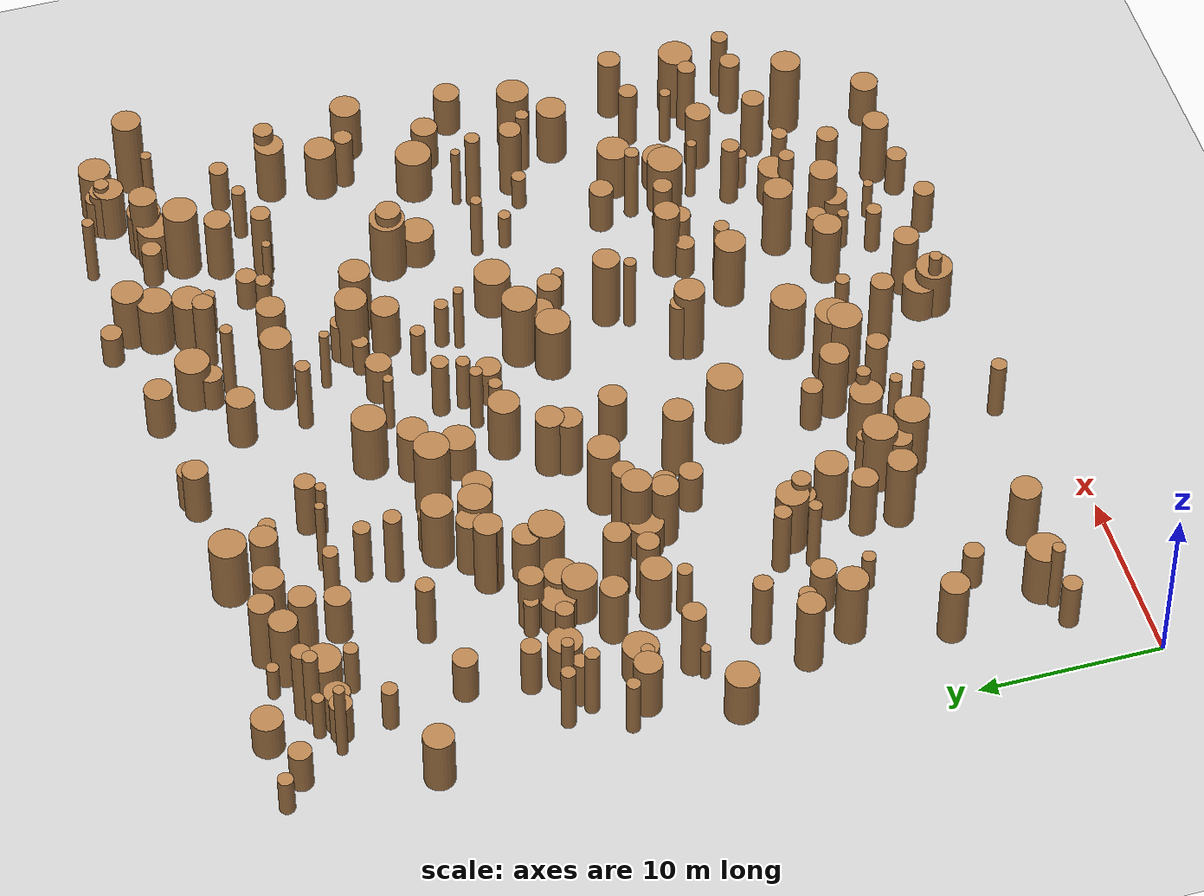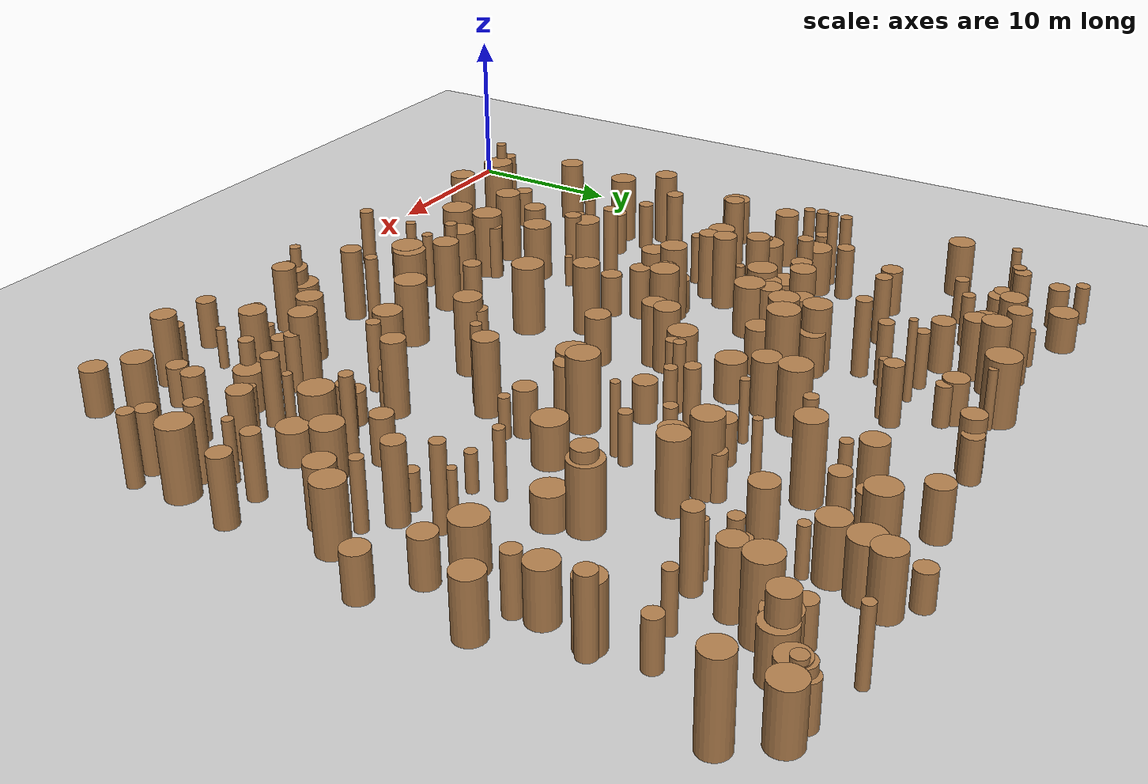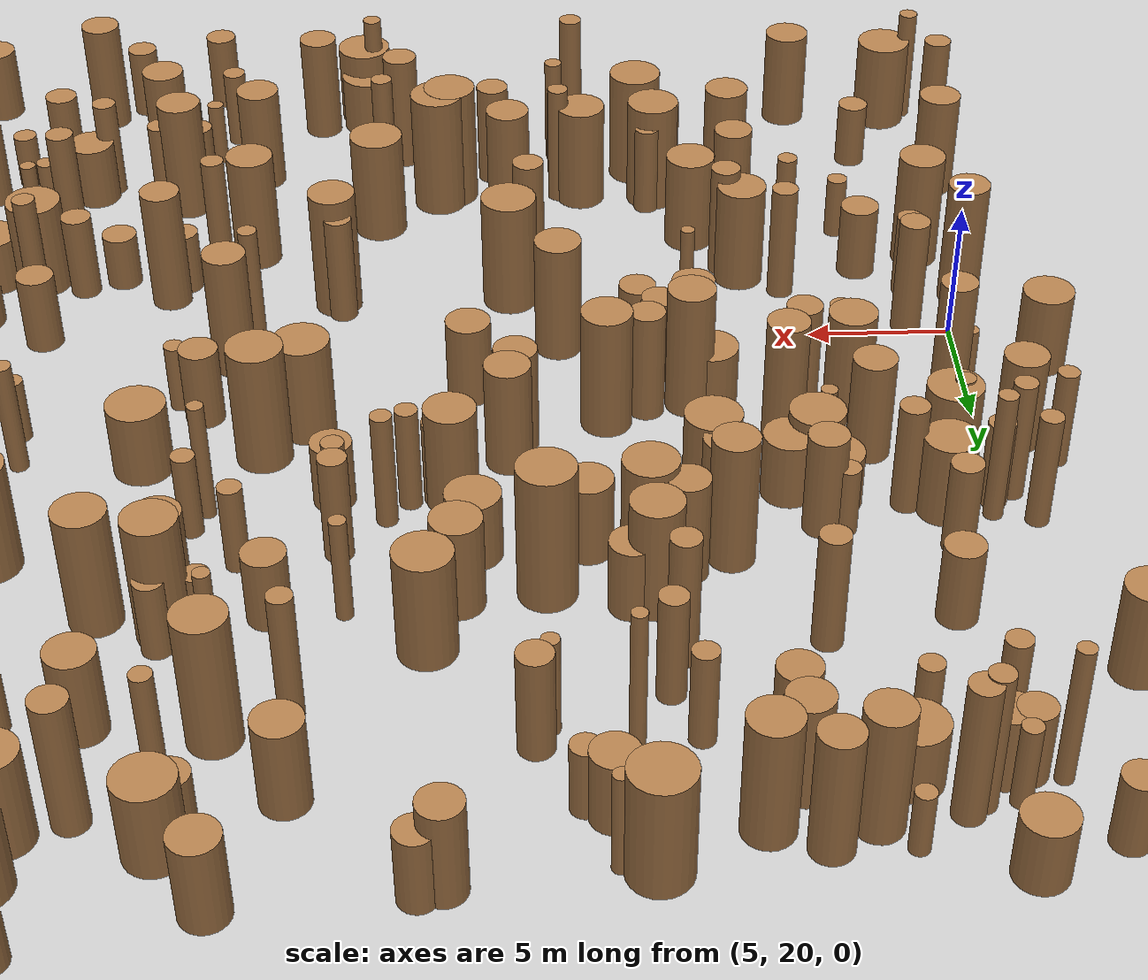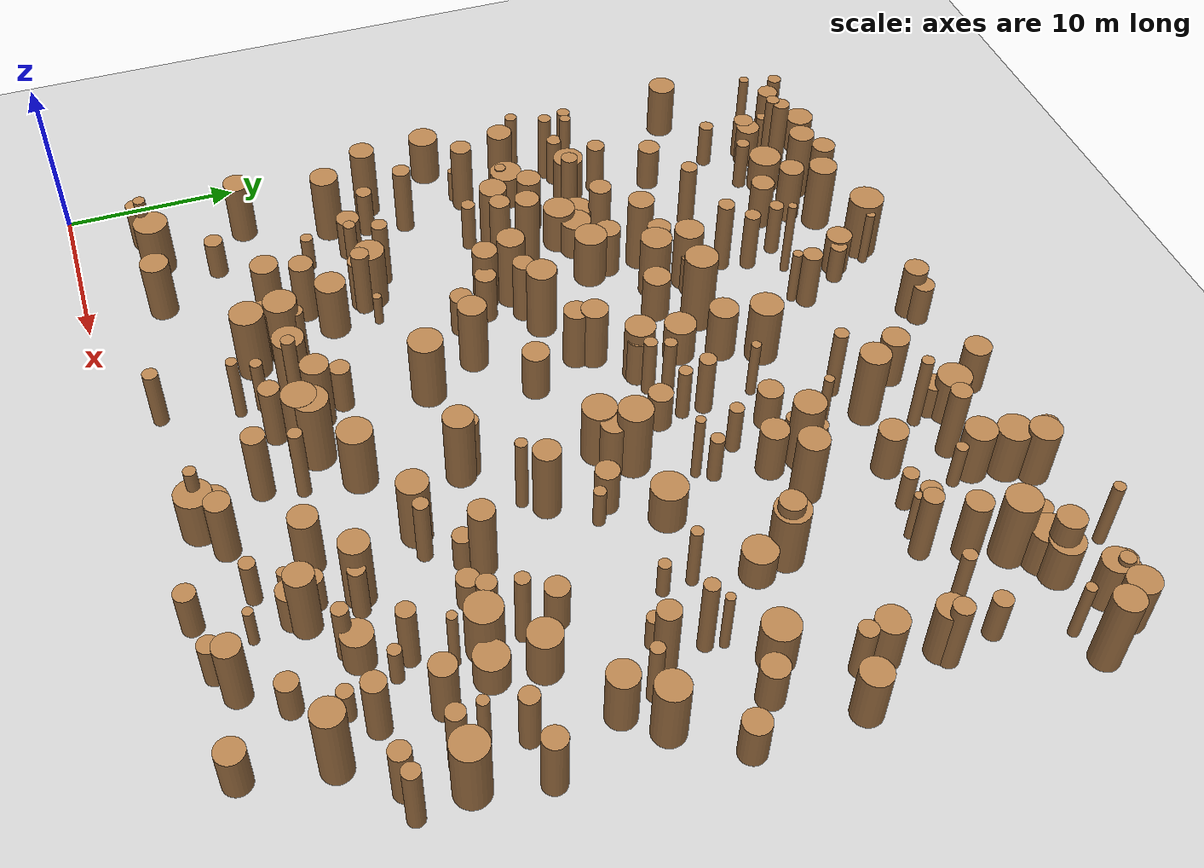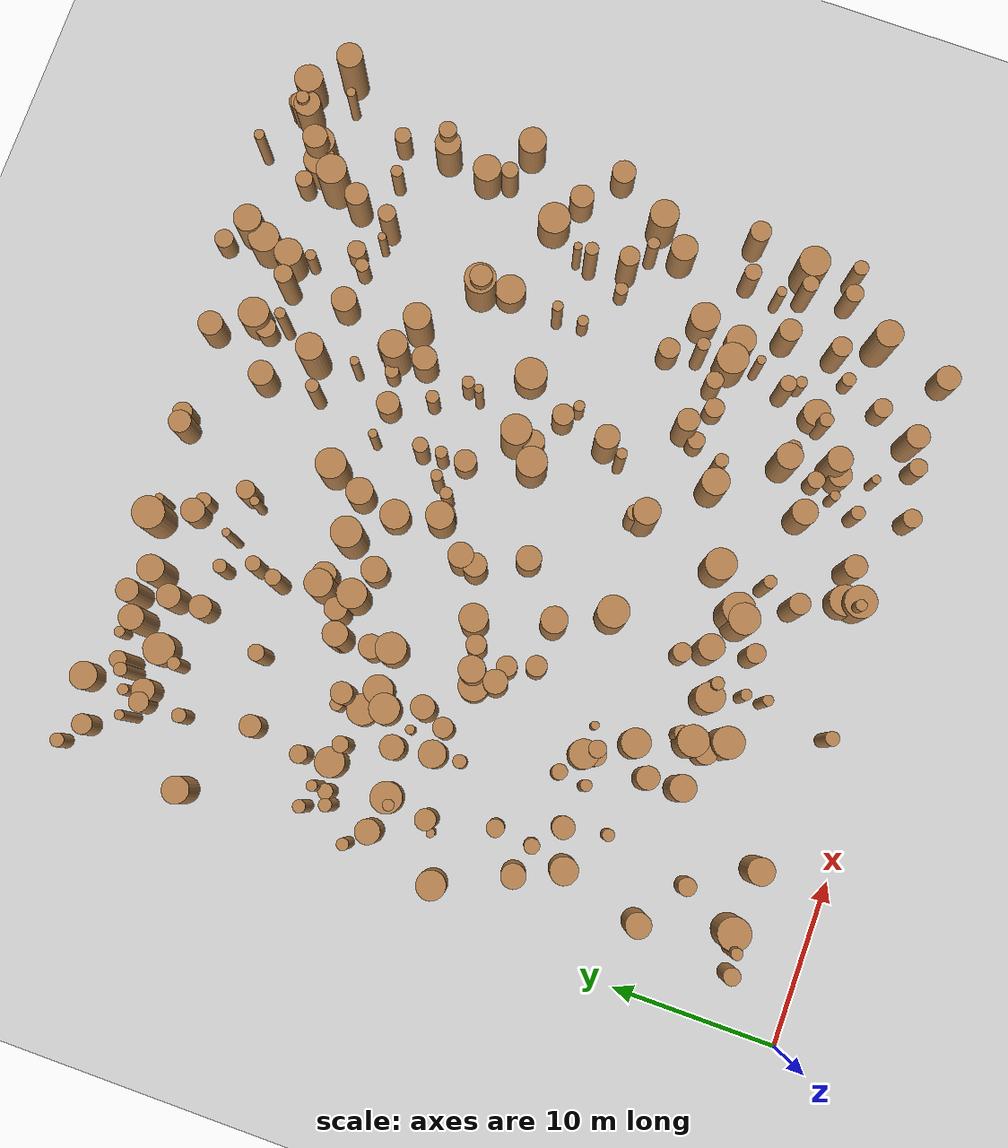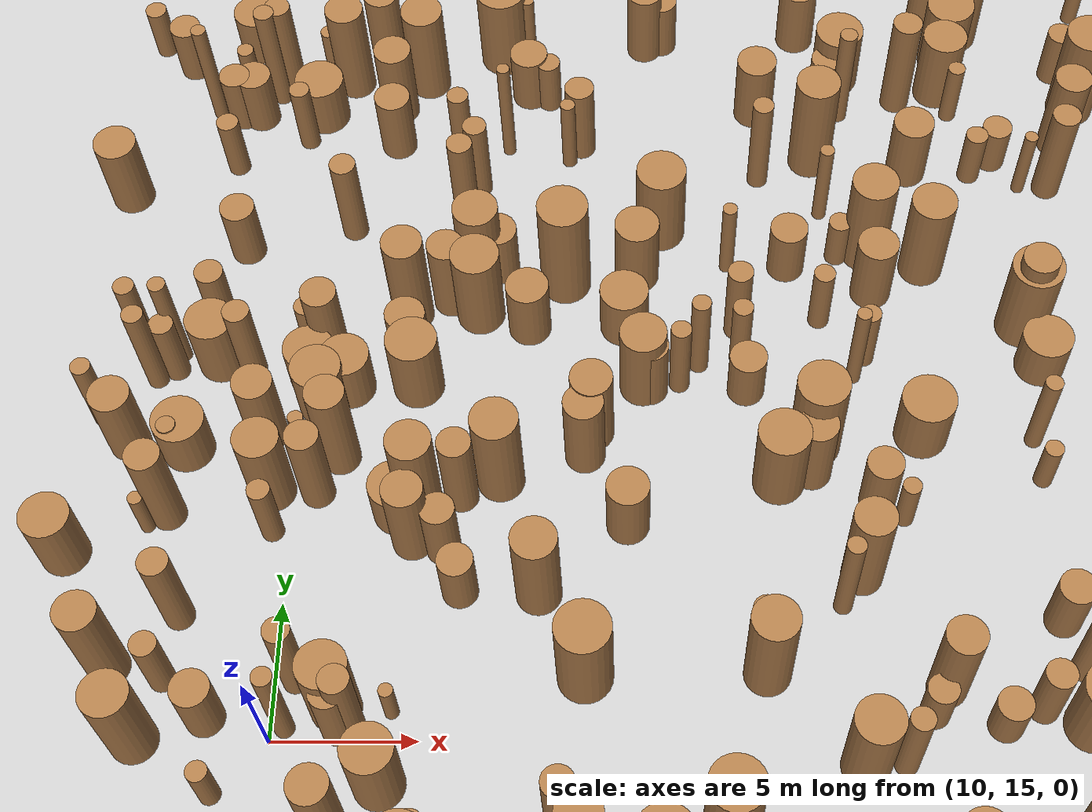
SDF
<?xml version="1.0"?>
<sdf version="1.6">
  <world name="PW_forest_seed0">
    <plugin name="static_transform_republisher" filename="libMrsGazeboCommonResources_StaticTransformRepublisher.so"/>
    <gravity>0 0 -9.80665</gravity>
    <physics name="mrs_ode_250hz" type="ode">
      <max_step_size>0.004</max_step_size>
      <real_time_factor>1.0</real_time_factor>
      <real_time_update_rate>250</real_time_update_rate>
    </physics>
    <scene>
      <ambient>0.4 0.4 0.4 1</ambient>
      <background>0.7 0.8 0.9 1</background>
      <shadows>true</shadows>
      <sky><clouds><speed>0.6</speed></clouds></sky>
    </scene>
    <include><uri>model://sun</uri></include>
    <include><uri>model://mid360_open_ground</uri><name>forest_ground</name></include>
    <include><uri>model://observer_rangefinder</uri></include>
    <model name="planning_forest_seed0">
      <static>true</static>
      <link name="tree_000"><pose>38.7282 38.0226 2.26028 0 -0 0</pose><collision name="collision"><geometry><cylinder><radius>0.545787</radius><length>4.52056</length></cylinder></geometry></collision><visual name="visual"><geometry><cylinder><radius>0.545787</radius><length>4.52056</length></cylinder></geometry><material><script><uri>file://media/materials/scripts/gazebo.material</uri><name>Gazebo/Wood</name></script></material></visual></link>
      <link name="tree_001"><pose>37.3386 17.4202 2.36747 0 -0 0</pose><collision name="collision"><geometry><cylinder><radius>0.398164</radius><length>4.73494</length></cylinder></geometry></collision><visual name="visual"><geometry><cylinder><radius>0.398164</radius><length>4.73494</length></cylinder></geometry><material><script><uri>file://media/materials/scripts/gazebo.material</uri><name>Gazebo/Wood</name></script></material></visual></link>
      <link name="tree_002"><pose>30.9281 23.9603 1.41666 0 -0 0</pose><collision name="collision"><geometry><cylinder><radius>0.665477</radius><length>2.83332</length></cylinder></geometry></collision><visual name="visual"><geometry><cylinder><radius>0.665477</radius><length>2.83332</length></cylinder></geometry><material><script><uri>file://media/materials/scripts/gazebo.material</uri><name>Gazebo/Wood</name></script></material></visual></link>
      <link name="tree_003"><pose>44.145 45.8026 1.54718 0 -0 0</pose><collision name="collision"><geometry><cylinder><radius>0.635051</radius><length>3.09435</length></cylinder></geometry></collision><visual name="visual"><geometry><cylinder><radius>0.635051</radius><length>3.09435</length></cylinder></geometry><material><script><uri>file://media/materials/scripts/gazebo.material</uri><name>Gazebo/Wood</name></script></material></visual></link>
      <link name="tree_004"><pose>29.9206 8.51372 1.95357 0 -0 0</pose><collision name="collision"><geometry><cylinder><radius>0.787973</radius><length>3.90714</length></cylinder></geometry></collision><visual name="visual"><geometry><cylinder><radius>0.787973</radius><length>3.90714</length></cylinder></geometry><material><script><uri>file://media/materials/scripts/gazebo.material</uri><name>Gazebo/Wood</name></script></material></visual></link>
      <link name="tree_005"><pose>38.9921 8.31265 1.02445 0 -0 0</pose><collision name="collision"><geometry><cylinder><radius>0.432165</radius><length>2.0489</length></cylinder></geometry></collision><visual name="visual"><geometry><cylinder><radius>0.432165</radius><length>2.0489</length></cylinder></geometry><material><script><uri>file://media/materials/scripts/gazebo.material</uri><name>Gazebo/Wood</name></script></material></visual></link>
      <link name="tree_006"><pose>7.0052 7.97036 1.23502 0 -0 0</pose><collision name="collision"><geometry><cylinder><radius>0.550708</radius><length>2.47004</length></cylinder></geometry></collision><visual name="visual"><geometry><cylinder><radius>0.550708</radius><length>2.47004</length></cylinder></geometry><material><script><uri>file://media/materials/scripts/gazebo.material</uri><name>Gazebo/Wood</name></script></material></visual></link>
      <link name="tree_007"><pose>40.5992 25.5949 2.49839 0 -0 0</pose><collision name="collision"><geometry><cylinder><radius>0.413693</radius><length>4.99677</length></cylinder></geometry></collision><visual name="visual"><geometry><cylinder><radius>0.413693</radius><length>4.99677</length></cylinder></geometry><material><script><uri>file://media/materials/scripts/gazebo.material</uri><name>Gazebo/Wood</name></script></material></visual></link>
      <link name="tree_008"><pose>26.1172 31.3274 1.91896 0 -0 0</pose><collision name="collision"><geometry><cylinder><radius>0.472024</radius><length>3.83792</length></cylinder></geometry></collision><visual name="visual"><geometry><cylinder><radius>0.472024</radius><length>3.83792</length></cylinder></geometry><material><script><uri>file://media/materials/scripts/gazebo.material</uri><name>Gazebo/Wood</name></script></material></visual></link>
      <link name="tree_009"><pose>37.4825 15.4558 1.74037 0 -0 0</pose><collision name="collision"><geometry><cylinder><radius>0.979581</radius><length>3.48075</length></cylinder></geometry></collision><visual name="visual"><geometry><cylinder><radius>0.979581</radius><length>3.48075</length></cylinder></geometry><material><script><uri>file://media/materials/scripts/gazebo.material</uri><name>Gazebo/Wood</name></script></material></visual></link>
      <link name="tree_010"><pose>43.0104 20.4105 1.79012 0 -0 0</pose><collision name="collision"><geometry><cylinder><radius>0.827435</radius><length>3.58024</length></cylinder></geometry></collision><visual name="visual"><geometry><cylinder><radius>0.827435</radius><length>3.58024</length></cylinder></geometry><material><script><uri>file://media/materials/scripts/gazebo.material</uri><name>Gazebo/Wood</name></script></material></visual></link>
      <link name="tree_011"><pose>44.2752 39.1553 1.42497 0 -0 0</pose><collision name="collision"><geometry><cylinder><radius>0.514344</radius><length>2.84994</length></cylinder></geometry></collision><visual name="visual"><geometry><cylinder><radius>0.514344</radius><length>2.84994</length></cylinder></geometry><material><script><uri>file://media/materials/scripts/gazebo.material</uri><name>Gazebo/Wood</name></script></material></visual></link>
      <link name="tree_012"><pose>5.95857 26.1958 1.10463 0 -0 0</pose><collision name="collision"><geometry><cylinder><radius>0.961995</radius><length>2.20927</length></cylinder></geometry></collision><visual name="visual"><geometry><cylinder><radius>0.961995</radius><length>2.20927</length></cylinder></geometry><material><script><uri>file://media/materials/scripts/gazebo.material</uri><name>Gazebo/Wood</name></script></material></visual></link>
      <link name="tree_013"><pose>18.0491 42.9507 1.28832 0 -0 0</pose><collision name="collision"><geometry><cylinder><radius>0.74742</radius><length>2.57664</length></cylinder></geometry></collision><visual name="visual"><geometry><cylinder><radius>0.74742</radius><length>2.57664</length></cylinder></geometry><material><script><uri>file://media/materials/scripts/gazebo.material</uri><name>Gazebo/Wood</name></script></material></visual></link>
      <link name="tree_014"><pose>4.90241 23.0543 1.09626 0 -0 0</pose><collision name="collision"><geometry><cylinder><radius>0.265017</radius><length>2.19251</length></cylinder></geometry></collision><visual name="visual"><geometry><cylinder><radius>0.265017</radius><length>2.19251</length></cylinder></geometry><material><script><uri>file://media/materials/scripts/gazebo.material</uri><name>Gazebo/Wood</name></script></material></visual></link>
      <link name="tree_015"><pose>41.1423 43.5016 1.35742 0 -0 0</pose><collision name="collision"><geometry><cylinder><radius>0.977976</radius><length>2.71484</length></cylinder></geometry></collision><visual name="visual"><geometry><cylinder><radius>0.977976</radius><length>2.71484</length></cylinder></geometry><material><script><uri>file://media/materials/scripts/gazebo.material</uri><name>Gazebo/Wood</name></script></material></visual></link>
      <link name="tree_016"><pose>36.9714 19.2595 1.4 0 -0 0</pose><collision name="collision"><geometry><cylinder><radius>0.65482</radius><length>2.8</length></cylinder></geometry></collision><visual name="visual"><geometry><cylinder><radius>0.65482</radius><length>2.8</length></cylinder></geometry><material><script><uri>file://media/materials/scripts/gazebo.material</uri><name>Gazebo/Wood</name></script></material></visual></link>
      <link name="tree_017"><pose>3.8069 26.4539 1.7688 0 -0 0</pose><collision name="collision"><geometry><cylinder><radius>0.750793</radius><length>3.53761</length></cylinder></geometry></collision><visual name="visual"><geometry><cylinder><radius>0.750793</radius><length>3.53761</length></cylinder></geometry><material><script><uri>file://media/materials/scripts/gazebo.material</uri><name>Gazebo/Wood</name></script></material></visual></link>
      <link name="tree_018"><pose>35.1638 44.8172 1.65646 0 -0 0</pose><collision name="collision"><geometry><cylinder><radius>0.948876</radius><length>3.31291</length></cylinder></geometry></collision><visual name="visual"><geometry><cylinder><radius>0.948876</radius><length>3.31291</length></cylinder></geometry><material><script><uri>file://media/materials/scripts/gazebo.material</uri><name>Gazebo/Wood</name></script></material></visual></link>
      <link name="tree_019"><pose>18.2862 31.439 1.42644 0 -0 0</pose><collision name="collision"><geometry><cylinder><radius>0.803901</radius><length>2.85288</length></cylinder></geometry></collision><visual name="visual"><geometry><cylinder><radius>0.803901</radius><length>2.85288</length></cylinder></geometry><material><script><uri>file://media/materials/scripts/gazebo.material</uri><name>Gazebo/Wood</name></script></material></visual></link>
      <link name="tree_020"><pose>42.4835 22.2448 2.03179 0 -0 0</pose><collision name="collision"><geometry><cylinder><radius>0.374481</radius><length>4.06358</length></cylinder></geometry></collision><visual name="visual"><geometry><cylinder><radius>0.374481</radius><length>4.06358</length></cylinder></geometry><material><script><uri>file://media/materials/scripts/gazebo.material</uri><name>Gazebo/Wood</name></script></material></visual></link>
      <link name="tree_021"><pose>43.0951 12.5325 2.2438 0 -0 0</pose><collision name="collision"><geometry><cylinder><radius>0.497753</radius><length>4.4876</length></cylinder></geometry></collision><visual name="visual"><geometry><cylinder><radius>0.497753</radius><length>4.4876</length></cylinder></geometry><material><script><uri>file://media/materials/scripts/gazebo.material</uri><name>Gazebo/Wood</name></script></material></visual></link>
      <link name="tree_022"><pose>29.0774 45.9975 1.52554 0 -0 0</pose><collision name="collision"><geometry><cylinder><radius>0.765002</radius><length>3.05108</length></cylinder></geometry></collision><visual name="visual"><geometry><cylinder><radius>0.765002</radius><length>3.05108</length></cylinder></geometry><material><script><uri>file://media/materials/scripts/gazebo.material</uri><name>Gazebo/Wood</name></script></material></visual></link>
      <link name="tree_023"><pose>44.5026 22.2198 1.98596 0 -0 0</pose><collision name="collision"><geometry><cylinder><radius>0.894007</radius><length>3.97191</length></cylinder></geometry></collision><visual name="visual"><geometry><cylinder><radius>0.894007</radius><length>3.97191</length></cylinder></geometry><material><script><uri>file://media/materials/scripts/gazebo.material</uri><name>Gazebo/Wood</name></script></material></visual></link>
      <link name="tree_024"><pose>43.9047 33.4741 1.59766 0 -0 0</pose><collision name="collision"><geometry><cylinder><radius>0.861075</radius><length>3.19531</length></cylinder></geometry></collision><visual name="visual"><geometry><cylinder><radius>0.861075</radius><length>3.19531</length></cylinder></geometry><material><script><uri>file://media/materials/scripts/gazebo.material</uri><name>Gazebo/Wood</name></script></material></visual></link>
      <link name="tree_025"><pose>44.3259 45.7116 1.72374 0 -0 0</pose><collision name="collision"><geometry><cylinder><radius>0.411869</radius><length>3.44747</length></cylinder></geometry></collision><visual name="visual"><geometry><cylinder><radius>0.411869</radius><length>3.44747</length></cylinder></geometry><material><script><uri>file://media/materials/scripts/gazebo.material</uri><name>Gazebo/Wood</name></script></material></visual></link>
      <link name="tree_026"><pose>21.8699 31.4897 1.22149 0 -0 0</pose><collision name="collision"><geometry><cylinder><radius>0.910797</radius><length>2.44298</length></cylinder></geometry></collision><visual name="visual"><geometry><cylinder><radius>0.910797</radius><length>2.44298</length></cylinder></geometry><material><script><uri>file://media/materials/scripts/gazebo.material</uri><name>Gazebo/Wood</name></script></material></visual></link>
      <link name="tree_027"><pose>16.1431 38.1561 1.92939 0 -0 0</pose><collision name="collision"><geometry><cylinder><radius>0.460795</radius><length>3.85879</length></cylinder></geometry></collision><visual name="visual"><geometry><cylinder><radius>0.460795</radius><length>3.85879</length></cylinder></geometry><material><script><uri>file://media/materials/scripts/gazebo.material</uri><name>Gazebo/Wood</name></script></material></visual></link>
      <link name="tree_028"><pose>14.7068 10.6265 1.67055 0 -0 0</pose><collision name="collision"><geometry><cylinder><radius>0.41958</radius><length>3.3411</length></cylinder></geometry></collision><visual name="visual"><geometry><cylinder><radius>0.41958</radius><length>3.3411</length></cylinder></geometry><material><script><uri>file://media/materials/scripts/gazebo.material</uri><name>Gazebo/Wood</name></script></material></visual></link>
      <link name="tree_029"><pose>43.713 9.80193 1.83467 0 -0 0</pose><collision name="collision"><geometry><cylinder><radius>0.562376</radius><length>3.66933</length></cylinder></geometry></collision><visual name="visual"><geometry><cylinder><radius>0.562376</radius><length>3.66933</length></cylinder></geometry><material><script><uri>file://media/materials/scripts/gazebo.material</uri><name>Gazebo/Wood</name></script></material></visual></link>
      <link name="tree_030"><pose>36.9819 24.7904 1.15476 0 -0 0</pose><collision name="collision"><geometry><cylinder><radius>0.344557</radius><length>2.30951</length></cylinder></geometry></collision><visual name="visual"><geometry><cylinder><radius>0.344557</radius><length>2.30951</length></cylinder></geometry><material><script><uri>file://media/materials/scripts/gazebo.material</uri><name>Gazebo/Wood</name></script></material></visual></link>
      <link name="tree_031"><pose>19.6267 33.4845 2.47713 0 -0 0</pose><collision name="collision"><geometry><cylinder><radius>0.951253</radius><length>4.95426</length></cylinder></geometry></collision><visual name="visual"><geometry><cylinder><radius>0.951253</radius><length>4.95426</length></cylinder></geometry><material><script><uri>file://media/materials/scripts/gazebo.material</uri><name>Gazebo/Wood</name></script></material></visual></link>
      <link name="tree_032"><pose>12.684 15.5314 2.12466 0 -0 0</pose><collision name="collision"><geometry><cylinder><radius>0.526498</radius><length>4.24931</length></cylinder></geometry></collision><visual name="visual"><geometry><cylinder><radius>0.526498</radius><length>4.24931</length></cylinder></geometry><material><script><uri>file://media/materials/scripts/gazebo.material</uri><name>Gazebo/Wood</name></script></material></visual></link>
      <link name="tree_033"><pose>35.6788 9.00993 1.87673 0 -0 0</pose><collision name="collision"><geometry><cylinder><radius>0.43331</radius><length>3.75347</length></cylinder></geometry></collision><visual name="visual"><geometry><cylinder><radius>0.43331</radius><length>3.75347</length></cylinder></geometry><material><script><uri>file://media/materials/scripts/gazebo.material</uri><name>Gazebo/Wood</name></script></material></visual></link>
      <link name="tree_034"><pose>36.2733 9.54869 1.18821 0 -0 0</pose><collision name="collision"><geometry><cylinder><radius>0.845103</radius><length>2.37642</length></cylinder></geometry></collision><visual name="visual"><geometry><cylinder><radius>0.845103</radius><length>2.37642</length></cylinder></geometry><material><script><uri>file://media/materials/scripts/gazebo.material</uri><name>Gazebo/Wood</name></script></material></visual></link>
      <link name="tree_035"><pose>25.9919 4.41635 1.11179 0 -0 0</pose><collision name="collision"><geometry><cylinder><radius>0.962578</radius><length>2.22359</length></cylinder></geometry></collision><visual name="visual"><geometry><cylinder><radius>0.962578</radius><length>2.22359</length></cylinder></geometry><material><script><uri>file://media/materials/scripts/gazebo.material</uri><name>Gazebo/Wood</name></script></material></visual></link>
      <link name="tree_036"><pose>35.7021 38.6987 1.26432 0 -0 0</pose><collision name="collision"><geometry><cylinder><radius>0.430047</radius><length>2.52863</length></cylinder></geometry></collision><visual name="visual"><geometry><cylinder><radius>0.430047</radius><length>2.52863</length></cylinder></geometry><material><script><uri>file://media/materials/scripts/gazebo.material</uri><name>Gazebo/Wood</name></script></material></visual></link>
      <link name="tree_037"><pose>36.9478 31.4151 1.98485 0 -0 0</pose><collision name="collision"><geometry><cylinder><radius>0.975554</radius><length>3.96969</length></cylinder></geometry></collision><visual name="visual"><geometry><cylinder><radius>0.975554</radius><length>3.96969</length></cylinder></geometry><material><script><uri>file://media/materials/scripts/gazebo.material</uri><name>Gazebo/Wood</name></script></material></visual></link>
      <link name="tree_038"><pose>5.59868 25.9297 1.14022 0 -0 0</pose><collision name="collision"><geometry><cylinder><radius>0.351177</radius><length>2.28044</length></cylinder></geometry></collision><visual name="visual"><geometry><cylinder><radius>0.351177</radius><length>2.28044</length></cylinder></geometry><material><script><uri>file://media/materials/scripts/gazebo.material</uri><name>Gazebo/Wood</name></script></material></visual></link>
      <link name="tree_039"><pose>39.7052 23.2253 1.10486 0 -0 0</pose><collision name="collision"><geometry><cylinder><radius>0.403491</radius><length>2.20972</length></cylinder></geometry></collision><visual name="visual"><geometry><cylinder><radius>0.403491</radius><length>2.20972</length></cylinder></geometry><material><script><uri>file://media/materials/scripts/gazebo.material</uri><name>Gazebo/Wood</name></script></material></visual></link>
      <link name="tree_040"><pose>9.25913 4.38919 1.85998 0 -0 0</pose><collision name="collision"><geometry><cylinder><radius>0.816686</radius><length>3.71996</length></cylinder></geometry></collision><visual name="visual"><geometry><cylinder><radius>0.816686</radius><length>3.71996</length></cylinder></geometry><material><script><uri>file://media/materials/scripts/gazebo.material</uri><name>Gazebo/Wood</name></script></material></visual></link>
      <link name="tree_041"><pose>7.77155 42.938 2.49999 0 -0 0</pose><collision name="collision"><geometry><cylinder><radius>0.403246</radius><length>4.99998</length></cylinder></geometry></collision><visual name="visual"><geometry><cylinder><radius>0.403246</radius><length>4.99998</length></cylinder></geometry><material><script><uri>file://media/materials/scripts/gazebo.material</uri><name>Gazebo/Wood</name></script></material></visual></link>
      <link name="tree_042"><pose>5.32712 42.0448 2.4967 0 -0 0</pose><collision name="collision"><geometry><cylinder><radius>0.290543</radius><length>4.9934</length></cylinder></geometry></collision><visual name="visual"><geometry><cylinder><radius>0.290543</radius><length>4.9934</length></cylinder></geometry><material><script><uri>file://media/materials/scripts/gazebo.material</uri><name>Gazebo/Wood</name></script></material></visual></link>
      <link name="tree_043"><pose>10.2971 29.319 1.00624 0 -0 0</pose><collision name="collision"><geometry><cylinder><radius>0.942302</radius><length>2.01248</length></cylinder></geometry></collision><visual name="visual"><geometry><cylinder><radius>0.942302</radius><length>2.01248</length></cylinder></geometry><material><script><uri>file://media/materials/scripts/gazebo.material</uri><name>Gazebo/Wood</name></script></material></visual></link>
      <link name="tree_044"><pose>39.706 43.9992 1.2447 0 -0 0</pose><collision name="collision"><geometry><cylinder><radius>0.543768</radius><length>2.48939</length></cylinder></geometry></collision><visual name="visual"><geometry><cylinder><radius>0.543768</radius><length>2.48939</length></cylinder></geometry><material><script><uri>file://media/materials/scripts/gazebo.material</uri><name>Gazebo/Wood</name></script></material></visual></link>
      <link name="tree_045"><pose>22.8185 28.6538 1.53864 0 -0 0</pose><collision name="collision"><geometry><cylinder><radius>0.664364</radius><length>3.07729</length></cylinder></geometry></collision><visual name="visual"><geometry><cylinder><radius>0.664364</radius><length>3.07729</length></cylinder></geometry><material><script><uri>file://media/materials/scripts/gazebo.material</uri><name>Gazebo/Wood</name></script></material></visual></link>
      <link name="tree_046"><pose>36.8355 26.4172 2.03108 0 -0 0</pose><collision name="collision"><geometry><cylinder><radius>0.32473</radius><length>4.06216</length></cylinder></geometry></collision><visual name="visual"><geometry><cylinder><radius>0.32473</radius><length>4.06216</length></cylinder></geometry><material><script><uri>file://media/materials/scripts/gazebo.material</uri><name>Gazebo/Wood</name></script></material></visual></link>
      <link name="tree_047"><pose>42.3702 28.5407 1.45644 0 -0 0</pose><collision name="collision"><geometry><cylinder><radius>0.994171</radius><length>2.91289</length></cylinder></geometry></collision><visual name="visual"><geometry><cylinder><radius>0.994171</radius><length>2.91289</length></cylinder></geometry><material><script><uri>file://media/materials/scripts/gazebo.material</uri><name>Gazebo/Wood</name></script></material></visual></link>
      <link name="tree_048"><pose>36.3989 3.62936 2.12171 0 -0 0</pose><collision name="collision"><geometry><cylinder><radius>0.721682</radius><length>4.24343</length></cylinder></geometry></collision><visual name="visual"><geometry><cylinder><radius>0.721682</radius><length>4.24343</length></cylinder></geometry><material><script><uri>file://media/materials/scripts/gazebo.material</uri><name>Gazebo/Wood</name></script></material></visual></link>
      <link name="tree_049"><pose>40.2277 42.1705 2.24986 0 -0 0</pose><collision name="collision"><geometry><cylinder><radius>0.944032</radius><length>4.49972</length></cylinder></geometry></collision><visual name="visual"><geometry><cylinder><radius>0.944032</radius><length>4.49972</length></cylinder></geometry><material><script><uri>file://media/materials/scripts/gazebo.material</uri><name>Gazebo/Wood</name></script></material></visual></link>
      <link name="tree_050"><pose>47.2454 43.5549 2.46915 0 -0 0</pose><collision name="collision"><geometry><cylinder><radius>0.807858</radius><length>4.9383</length></cylinder></geometry></collision><visual name="visual"><geometry><cylinder><radius>0.807858</radius><length>4.9383</length></cylinder></geometry><material><script><uri>file://media/materials/scripts/gazebo.material</uri><name>Gazebo/Wood</name></script></material></visual></link>
      <link name="tree_051"><pose>40.1805 9.54253 2.00032 0 -0 0</pose><collision name="collision"><geometry><cylinder><radius>0.622944</radius><length>4.00064</length></cylinder></geometry></collision><visual name="visual"><geometry><cylinder><radius>0.622944</radius><length>4.00064</length></cylinder></geometry><material><script><uri>file://media/materials/scripts/gazebo.material</uri><name>Gazebo/Wood</name></script></material></visual></link>
      <link name="tree_052"><pose>13.41 31.8865 2.33342 0 -0 0</pose><collision name="collision"><geometry><cylinder><radius>0.307746</radius><length>4.66685</length></cylinder></geometry></collision><visual name="visual"><geometry><cylinder><radius>0.307746</radius><length>4.66685</length></cylinder></geometry><material><script><uri>file://media/materials/scripts/gazebo.material</uri><name>Gazebo/Wood</name></script></material></visual></link>
      <link name="tree_053"><pose>16.5759 34.2285 1.94422 0 -0 0</pose><collision name="collision"><geometry><cylinder><radius>0.421853</radius><length>3.88844</length></cylinder></geometry></collision><visual name="visual"><geometry><cylinder><radius>0.421853</radius><length>3.88844</length></cylinder></geometry><material><script><uri>file://media/materials/scripts/gazebo.material</uri><name>Gazebo/Wood</name></script></material></visual></link>
      <link name="tree_054"><pose>31.1213 5.4114 1.49317 0 -0 0</pose><collision name="collision"><geometry><cylinder><radius>0.423571</radius><length>2.98633</length></cylinder></geometry></collision><visual name="visual"><geometry><cylinder><radius>0.423571</radius><length>2.98633</length></cylinder></geometry><material><script><uri>file://media/materials/scripts/gazebo.material</uri><name>Gazebo/Wood</name></script></material></visual></link>
      <link name="tree_055"><pose>46.6874 25.4916 1.33548 0 -0 0</pose><collision name="collision"><geometry><cylinder><radius>0.738349</radius><length>2.67097</length></cylinder></geometry></collision><visual name="visual"><geometry><cylinder><radius>0.738349</radius><length>2.67097</length></cylinder></geometry><material><script><uri>file://media/materials/scripts/gazebo.material</uri><name>Gazebo/Wood</name></script></material></visual></link>
      <link name="tree_056"><pose>7.21091 35.0864 1.42006 0 -0 0</pose><collision name="collision"><geometry><cylinder><radius>0.65958</radius><length>2.84013</length></cylinder></geometry></collision><visual name="visual"><geometry><cylinder><radius>0.65958</radius><length>2.84013</length></cylinder></geometry><material><script><uri>file://media/materials/scripts/gazebo.material</uri><name>Gazebo/Wood</name></script></material></visual></link>
      <link name="tree_057"><pose>22.7422 45.4386 1.70723 0 -0 0</pose><collision name="collision"><geometry><cylinder><radius>0.694405</radius><length>3.41445</length></cylinder></geometry></collision><visual name="visual"><geometry><cylinder><radius>0.694405</radius><length>3.41445</length></cylinder></geometry><material><script><uri>file://media/materials/scripts/gazebo.material</uri><name>Gazebo/Wood</name></script></material></visual></link>
      <link name="tree_058"><pose>2.14865 21.9876 1.50453 0 -0 0</pose><collision name="collision"><geometry><cylinder><radius>0.885763</radius><length>3.00905</length></cylinder></geometry></collision><visual name="visual"><geometry><cylinder><radius>0.885763</radius><length>3.00905</length></cylinder></geometry><material><script><uri>file://media/materials/scripts/gazebo.material</uri><name>Gazebo/Wood</name></script></material></visual></link>
      <link name="tree_059"><pose>12.759 40.3292 1.51741 0 -0 0</pose><collision name="collision"><geometry><cylinder><radius>0.698861</radius><length>3.03483</length></cylinder></geometry></collision><visual name="visual"><geometry><cylinder><radius>0.698861</radius><length>3.03483</length></cylinder></geometry><material><script><uri>file://media/materials/scripts/gazebo.material</uri><name>Gazebo/Wood</name></script></material></visual></link>
      <link name="tree_060"><pose>16.028 24.169 2.01321 0 -0 0</pose><collision name="collision"><geometry><cylinder><radius>0.612213</radius><length>4.02643</length></cylinder></geometry></collision><visual name="visual"><geometry><cylinder><radius>0.612213</radius><length>4.02643</length></cylinder></geometry><material><script><uri>file://media/materials/scripts/gazebo.material</uri><name>Gazebo/Wood</name></script></material></visual></link>
      <link name="tree_061"><pose>3.87976 30.6038 2.06813 0 -0 0</pose><collision name="collision"><geometry><cylinder><radius>0.386917</radius><length>4.13626</length></cylinder></geometry></collision><visual name="visual"><geometry><cylinder><radius>0.386917</radius><length>4.13626</length></cylinder></geometry><material><script><uri>file://media/materials/scripts/gazebo.material</uri><name>Gazebo/Wood</name></script></material></visual></link>
      <link name="tree_062"><pose>31.3314 33.0011 1.62098 0 -0 0</pose><collision name="collision"><geometry><cylinder><radius>0.771988</radius><length>3.24195</length></cylinder></geometry></collision><visual name="visual"><geometry><cylinder><radius>0.771988</radius><length>3.24195</length></cylinder></geometry><material><script><uri>file://media/materials/scripts/gazebo.material</uri><name>Gazebo/Wood</name></script></material></visual></link>
      <link name="tree_063"><pose>30.8493 30.0189 1.52067 0 -0 0</pose><collision name="collision"><geometry><cylinder><radius>0.388467</radius><length>3.04135</length></cylinder></geometry></collision><visual name="visual"><geometry><cylinder><radius>0.388467</radius><length>3.04135</length></cylinder></geometry><material><script><uri>file://media/materials/scripts/gazebo.material</uri><name>Gazebo/Wood</name></script></material></visual></link>
      <link name="tree_064"><pose>11.3018 36.0602 2.09609 0 -0 0</pose><collision name="collision"><geometry><cylinder><radius>0.496281</radius><length>4.19219</length></cylinder></geometry></collision><visual name="visual"><geometry><cylinder><radius>0.496281</radius><length>4.19219</length></cylinder></geometry><material><script><uri>file://media/materials/scripts/gazebo.material</uri><name>Gazebo/Wood</name></script></material></visual></link>
      <link name="tree_065"><pose>13.8342 32.044 2.38137 0 -0 0</pose><collision name="collision"><geometry><cylinder><radius>0.763567</radius><length>4.76274</length></cylinder></geometry></collision><visual name="visual"><geometry><cylinder><radius>0.763567</radius><length>4.76274</length></cylinder></geometry><material><script><uri>file://media/materials/scripts/gazebo.material</uri><name>Gazebo/Wood</name></script></material></visual></link>
      <link name="tree_066"><pose>42.3597 13.9829 1.79866 0 -0 0</pose><collision name="collision"><geometry><cylinder><radius>0.315733</radius><length>3.59732</length></cylinder></geometry></collision><visual name="visual"><geometry><cylinder><radius>0.315733</radius><length>3.59732</length></cylinder></geometry><material><script><uri>file://media/materials/scripts/gazebo.material</uri><name>Gazebo/Wood</name></script></material></visual></link>
      <link name="tree_067"><pose>18.6336 7.11868 2.02919 0 -0 0</pose><collision name="collision"><geometry><cylinder><radius>0.320305</radius><length>4.05837</length></cylinder></geometry></collision><visual name="visual"><geometry><cylinder><radius>0.320305</radius><length>4.05837</length></cylinder></geometry><material><script><uri>file://media/materials/scripts/gazebo.material</uri><name>Gazebo/Wood</name></script></material></visual></link>
      <link name="tree_068"><pose>15.2838 32.6616 1.86504 0 -0 0</pose><collision name="collision"><geometry><cylinder><radius>0.694909</radius><length>3.73007</length></cylinder></geometry></collision><visual name="visual"><geometry><cylinder><radius>0.694909</radius><length>3.73007</length></cylinder></geometry><material><script><uri>file://media/materials/scripts/gazebo.material</uri><name>Gazebo/Wood</name></script></material></visual></link>
      <link name="tree_069"><pose>10.7285 17.1635 2.16365 0 -0 0</pose><collision name="collision"><geometry><cylinder><radius>0.466285</radius><length>4.3273</length></cylinder></geometry></collision><visual name="visual"><geometry><cylinder><radius>0.466285</radius><length>4.3273</length></cylinder></geometry><material><script><uri>file://media/materials/scripts/gazebo.material</uri><name>Gazebo/Wood</name></script></material></visual></link>
      <link name="tree_070"><pose>17.248 40.06 2.47654 0 -0 0</pose><collision name="collision"><geometry><cylinder><radius>0.252684</radius><length>4.95309</length></cylinder></geometry></collision><visual name="visual"><geometry><cylinder><radius>0.252684</radius><length>4.95309</length></cylinder></geometry><material><script><uri>file://media/materials/scripts/gazebo.material</uri><name>Gazebo/Wood</name></script></material></visual></link>
      <link name="tree_071"><pose>44.2708 46.0973 1.2823 0 -0 0</pose><collision name="collision"><geometry><cylinder><radius>0.577373</radius><length>2.5646</length></cylinder></geometry></collision><visual name="visual"><geometry><cylinder><radius>0.577373</radius><length>2.5646</length></cylinder></geometry><material><script><uri>file://media/materials/scripts/gazebo.material</uri><name>Gazebo/Wood</name></script></material></visual></link>
      <link name="tree_072"><pose>33.5461 7.57259 2.14731 0 -0 0</pose><collision name="collision"><geometry><cylinder><radius>0.774307</radius><length>4.29461</length></cylinder></geometry></collision><visual name="visual"><geometry><cylinder><radius>0.774307</radius><length>4.29461</length></cylinder></geometry><material><script><uri>file://media/materials/scripts/gazebo.material</uri><name>Gazebo/Wood</name></script></material></visual></link>
      <link name="tree_073"><pose>44.1486 45.3804 1.57575 0 -0 0</pose><collision name="collision"><geometry><cylinder><radius>0.830705</radius><length>3.1515</length></cylinder></geometry></collision><visual name="visual"><geometry><cylinder><radius>0.830705</radius><length>3.1515</length></cylinder></geometry><material><script><uri>file://media/materials/scripts/gazebo.material</uri><name>Gazebo/Wood</name></script></material></visual></link>
      <link name="tree_074"><pose>27.2099 38.5082 2.29288 0 -0 0</pose><collision name="collision"><geometry><cylinder><radius>0.402661</radius><length>4.58575</length></cylinder></geometry></collision><visual name="visual"><geometry><cylinder><radius>0.402661</radius><length>4.58575</length></cylinder></geometry><material><script><uri>file://media/materials/scripts/gazebo.material</uri><name>Gazebo/Wood</name></script></material></visual></link>
      <link name="tree_075"><pose>42.203 43.8436 1.44593 0 -0 0</pose><collision name="collision"><geometry><cylinder><radius>0.928699</radius><length>2.89187</length></cylinder></geometry></collision><visual name="visual"><geometry><cylinder><radius>0.928699</radius><length>2.89187</length></cylinder></geometry><material><script><uri>file://media/materials/scripts/gazebo.material</uri><name>Gazebo/Wood</name></script></material></visual></link>
      <link name="tree_076"><pose>14.5999 9.48681 1.74722 0 -0 0</pose><collision name="collision"><geometry><cylinder><radius>0.68215</radius><length>3.49443</length></cylinder></geometry></collision><visual name="visual"><geometry><cylinder><radius>0.68215</radius><length>3.49443</length></cylinder></geometry><material><script><uri>file://media/materials/scripts/gazebo.material</uri><name>Gazebo/Wood</name></script></material></visual></link>
      <link name="tree_077"><pose>41.0513 23.3285 2.29687 0 -0 0</pose><collision name="collision"><geometry><cylinder><radius>0.619299</radius><length>4.59374</length></cylinder></geometry></collision><visual name="visual"><geometry><cylinder><radius>0.619299</radius><length>4.59374</length></cylinder></geometry><material><script><uri>file://media/materials/scripts/gazebo.material</uri><name>Gazebo/Wood</name></script></material></visual></link>
      <link name="tree_078"><pose>33.4722 10.2994 1.74397 0 -0 0</pose><collision name="collision"><geometry><cylinder><radius>0.46829</radius><length>3.48793</length></cylinder></geometry></collision><visual name="visual"><geometry><cylinder><radius>0.46829</radius><length>3.48793</length></cylinder></geometry><material><script><uri>file://media/materials/scripts/gazebo.material</uri><name>Gazebo/Wood</name></script></material></visual></link>
      <link name="tree_079"><pose>24.6514 29.743 2.09133 0 -0 0</pose><collision name="collision"><geometry><cylinder><radius>0.354294</radius><length>4.18265</length></cylinder></geometry></collision><visual name="visual"><geometry><cylinder><radius>0.354294</radius><length>4.18265</length></cylinder></geometry><material><script><uri>file://media/materials/scripts/gazebo.material</uri><name>Gazebo/Wood</name></script></material></visual></link>
      <link name="tree_080"><pose>12.2104 10.1975 2.2572 0 -0 0</pose><collision name="collision"><geometry><cylinder><radius>0.793189</radius><length>4.5144</length></cylinder></geometry></collision><visual name="visual"><geometry><cylinder><radius>0.793189</radius><length>4.5144</length></cylinder></geometry><material><script><uri>file://media/materials/scripts/gazebo.material</uri><name>Gazebo/Wood</name></script></material></visual></link>
      <link name="tree_081"><pose>18.5804 8.35897 1.74779 0 -0 0</pose><collision name="collision"><geometry><cylinder><radius>0.340944</radius><length>3.49558</length></cylinder></geometry></collision><visual name="visual"><geometry><cylinder><radius>0.340944</radius><length>3.49558</length></cylinder></geometry><material><script><uri>file://media/materials/scripts/gazebo.material</uri><name>Gazebo/Wood</name></script></material></visual></link>
      <link name="tree_082"><pose>30.6164 43.7903 1.48721 0 -0 0</pose><collision name="collision"><geometry><cylinder><radius>0.948921</radius><length>2.97442</length></cylinder></geometry></collision><visual name="visual"><geometry><cylinder><radius>0.948921</radius><length>2.97442</length></cylinder></geometry><material><script><uri>file://media/materials/scripts/gazebo.material</uri><name>Gazebo/Wood</name></script></material></visual></link>
      <link name="tree_083"><pose>17.4087 24.8194 2.25524 0 -0 0</pose><collision name="collision"><geometry><cylinder><radius>0.863596</radius><length>4.51048</length></cylinder></geometry></collision><visual name="visual"><geometry><cylinder><radius>0.863596</radius><length>4.51048</length></cylinder></geometry><material><script><uri>file://media/materials/scripts/gazebo.material</uri><name>Gazebo/Wood</name></script></material></visual></link>
      <link name="tree_084"><pose>13.9097 30.0086 1.59149 0 -0 0</pose><collision name="collision"><geometry><cylinder><radius>0.744123</radius><length>3.18298</length></cylinder></geometry></collision><visual name="visual"><geometry><cylinder><radius>0.744123</radius><length>3.18298</length></cylinder></geometry><material><script><uri>file://media/materials/scripts/gazebo.material</uri><name>Gazebo/Wood</name></script></material></visual></link>
      <link name="tree_085"><pose>31.7715 6.96102 1.22685 0 -0 0</pose><collision name="collision"><geometry><cylinder><radius>0.304409</radius><length>2.45369</length></cylinder></geometry></collision><visual name="visual"><geometry><cylinder><radius>0.304409</radius><length>2.45369</length></cylinder></geometry><material><script><uri>file://media/materials/scripts/gazebo.material</uri><name>Gazebo/Wood</name></script></material></visual></link>
      <link name="tree_086"><pose>6.19283 17.2437 1.5454 0 -0 0</pose><collision name="collision"><geometry><cylinder><radius>0.466202</radius><length>3.09079</length></cylinder></geometry></collision><visual name="visual"><geometry><cylinder><radius>0.466202</radius><length>3.09079</length></cylinder></geometry><material><script><uri>file://media/materials/scripts/gazebo.material</uri><name>Gazebo/Wood</name></script></material></visual></link>
      <link name="tree_087"><pose>14.2112 28.8442 1.64099 0 -0 0</pose><collision name="collision"><geometry><cylinder><radius>0.950871</radius><length>3.28198</length></cylinder></geometry></collision><visual name="visual"><geometry><cylinder><radius>0.950871</radius><length>3.28198</length></cylinder></geometry><material><script><uri>file://media/materials/scripts/gazebo.material</uri><name>Gazebo/Wood</name></script></material></visual></link>
      <link name="tree_088"><pose>9.23452 24.4216 1.98812 0 -0 0</pose><collision name="collision"><geometry><cylinder><radius>0.821333</radius><length>3.97624</length></cylinder></geometry></collision><visual name="visual"><geometry><cylinder><radius>0.821333</radius><length>3.97624</length></cylinder></geometry><material><script><uri>file://media/materials/scripts/gazebo.material</uri><name>Gazebo/Wood</name></script></material></visual></link>
      <link name="tree_089"><pose>11.5608 25.8149 2.32455 0 -0 0</pose><collision name="collision"><geometry><cylinder><radius>0.719249</radius><length>4.64911</length></cylinder></geometry></collision><visual name="visual"><geometry><cylinder><radius>0.719249</radius><length>4.64911</length></cylinder></geometry><material><script><uri>file://media/materials/scripts/gazebo.material</uri><name>Gazebo/Wood</name></script></material></visual></link>
      <link name="tree_090"><pose>20.1419 40.1772 1.83634 0 -0 0</pose><collision name="collision"><geometry><cylinder><radius>0.56965</radius><length>3.67268</length></cylinder></geometry></collision><visual name="visual"><geometry><cylinder><radius>0.56965</radius><length>3.67268</length></cylinder></geometry><material><script><uri>file://media/materials/scripts/gazebo.material</uri><name>Gazebo/Wood</name></script></material></visual></link>
      <link name="tree_091"><pose>31.3781 35.5506 1.36649 0 -0 0</pose><collision name="collision"><geometry><cylinder><radius>0.49451</radius><length>2.73298</length></cylinder></geometry></collision><visual name="visual"><geometry><cylinder><radius>0.49451</radius><length>2.73298</length></cylinder></geometry><material><script><uri>file://media/materials/scripts/gazebo.material</uri><name>Gazebo/Wood</name></script></material></visual></link>
      <link name="tree_092"><pose>8.25943 43.2878 2.47727 0 -0 0</pose><collision name="collision"><geometry><cylinder><radius>0.503682</radius><length>4.95453</length></cylinder></geometry></collision><visual name="visual"><geometry><cylinder><radius>0.503682</radius><length>4.95453</length></cylinder></geometry><material><script><uri>file://media/materials/scripts/gazebo.material</uri><name>Gazebo/Wood</name></script></material></visual></link>
      <link name="tree_093"><pose>37.6218 38.031 1.61618 0 -0 0</pose><collision name="collision"><geometry><cylinder><radius>0.254056</radius><length>3.23236</length></cylinder></geometry></collision><visual name="visual"><geometry><cylinder><radius>0.254056</radius><length>3.23236</length></cylinder></geometry><material><script><uri>file://media/materials/scripts/gazebo.material</uri><name>Gazebo/Wood</name></script></material></visual></link>
      <link name="tree_094"><pose>35.1663 41.8146 1.44052 0 -0 0</pose><collision name="collision"><geometry><cylinder><radius>0.336001</radius><length>2.88103</length></cylinder></geometry></collision><visual name="visual"><geometry><cylinder><radius>0.336001</radius><length>2.88103</length></cylinder></geometry><material><script><uri>file://media/materials/scripts/gazebo.material</uri><name>Gazebo/Wood</name></script></material></visual></link>
      <link name="tree_095"><pose>34.5638 47.3775 1.07374 0 -0 0</pose><collision name="collision"><geometry><cylinder><radius>0.586829</radius><length>2.14749</length></cylinder></geometry></collision><visual name="visual"><geometry><cylinder><radius>0.586829</radius><length>2.14749</length></cylinder></geometry><material><script><uri>file://media/materials/scripts/gazebo.material</uri><name>Gazebo/Wood</name></script></material></visual></link>
      <link name="tree_096"><pose>6.3203 41.7983 1.31632 0 -0 0</pose><collision name="collision"><geometry><cylinder><radius>0.60542</radius><length>2.63265</length></cylinder></geometry></collision><visual name="visual"><geometry><cylinder><radius>0.60542</radius><length>2.63265</length></cylinder></geometry><material><script><uri>file://media/materials/scripts/gazebo.material</uri><name>Gazebo/Wood</name></script></material></visual></link>
      <link name="tree_097"><pose>32.2275 15.8811 1.14934 0 -0 0</pose><collision name="collision"><geometry><cylinder><radius>0.537172</radius><length>2.29868</length></cylinder></geometry></collision><visual name="visual"><geometry><cylinder><radius>0.537172</radius><length>2.29868</length></cylinder></geometry><material><script><uri>file://media/materials/scripts/gazebo.material</uri><name>Gazebo/Wood</name></script></material></visual></link>
      <link name="tree_098"><pose>4.45743 4.36938 2.21364 0 -0 0</pose><collision name="collision"><geometry><cylinder><radius>0.348777</radius><length>4.42729</length></cylinder></geometry></collision><visual name="visual"><geometry><cylinder><radius>0.348777</radius><length>4.42729</length></cylinder></geometry><material><script><uri>file://media/materials/scripts/gazebo.material</uri><name>Gazebo/Wood</name></script></material></visual></link>
      <link name="tree_099"><pose>22.3578 33.8355 1.68657 0 -0 0</pose><collision name="collision"><geometry><cylinder><radius>0.835651</radius><length>3.37315</length></cylinder></geometry></collision><visual name="visual"><geometry><cylinder><radius>0.835651</radius><length>3.37315</length></cylinder></geometry><material><script><uri>file://media/materials/scripts/gazebo.material</uri><name>Gazebo/Wood</name></script></material></visual></link>
      <link name="tree_100"><pose>26.3754 28.6172 1.17867 0 -0 0</pose><collision name="collision"><geometry><cylinder><radius>0.692228</radius><length>2.35733</length></cylinder></geometry></collision><visual name="visual"><geometry><cylinder><radius>0.692228</radius><length>2.35733</length></cylinder></geometry><material><script><uri>file://media/materials/scripts/gazebo.material</uri><name>Gazebo/Wood</name></script></material></visual></link>
      <link name="tree_101"><pose>42.8813 15.9971 1.89257 0 -0 0</pose><collision name="collision"><geometry><cylinder><radius>0.521438</radius><length>3.78514</length></cylinder></geometry></collision><visual name="visual"><geometry><cylinder><radius>0.521438</radius><length>3.78514</length></cylinder></geometry><material><script><uri>file://media/materials/scripts/gazebo.material</uri><name>Gazebo/Wood</name></script></material></visual></link>
      <link name="tree_102"><pose>26.1844 30.0475 1.71488 0 -0 0</pose><collision name="collision"><geometry><cylinder><radius>0.377365</radius><length>3.42975</length></cylinder></geometry></collision><visual name="visual"><geometry><cylinder><radius>0.377365</radius><length>3.42975</length></cylinder></geometry><material><script><uri>file://media/materials/scripts/gazebo.material</uri><name>Gazebo/Wood</name></script></material></visual></link>
      <link name="tree_103"><pose>40.1712 12.7482 1.92839 0 -0 0</pose><collision name="collision"><geometry><cylinder><radius>0.697147</radius><length>3.85678</length></cylinder></geometry></collision><visual name="visual"><geometry><cylinder><radius>0.697147</radius><length>3.85678</length></cylinder></geometry><material><script><uri>file://media/materials/scripts/gazebo.material</uri><name>Gazebo/Wood</name></script></material></visual></link>
      <link name="tree_104"><pose>9.80388 44.4915 1.10514 0 -0 0</pose><collision name="collision"><geometry><cylinder><radius>0.324128</radius><length>2.21027</length></cylinder></geometry></collision><visual name="visual"><geometry><cylinder><radius>0.324128</radius><length>2.21027</length></cylinder></geometry><material><script><uri>file://media/materials/scripts/gazebo.material</uri><name>Gazebo/Wood</name></script></material></visual></link>
      <link name="tree_105"><pose>15.3781 40.0314 1.7226 0 -0 0</pose><collision name="collision"><geometry><cylinder><radius>0.419118</radius><length>3.4452</length></cylinder></geometry></collision><visual name="visual"><geometry><cylinder><radius>0.419118</radius><length>3.4452</length></cylinder></geometry><material><script><uri>file://media/materials/scripts/gazebo.material</uri><name>Gazebo/Wood</name></script></material></visual></link>
      <link name="tree_106"><pose>39.4858 17.8355 1.53579 0 -0 0</pose><collision name="collision"><geometry><cylinder><radius>0.908708</radius><length>3.07158</length></cylinder></geometry></collision><visual name="visual"><geometry><cylinder><radius>0.908708</radius><length>3.07158</length></cylinder></geometry><material><script><uri>file://media/materials/scripts/gazebo.material</uri><name>Gazebo/Wood</name></script></material></visual></link>
      <link name="tree_107"><pose>37.7998 13.8436 1.98872 0 -0 0</pose><collision name="collision"><geometry><cylinder><radius>0.277246</radius><length>3.97744</length></cylinder></geometry></collision><visual name="visual"><geometry><cylinder><radius>0.277246</radius><length>3.97744</length></cylinder></geometry><material><script><uri>file://media/materials/scripts/gazebo.material</uri><name>Gazebo/Wood</name></script></material></visual></link>
      <link name="tree_108"><pose>12.1664 16.1752 1.93895 0 -0 0</pose><collision name="collision"><geometry><cylinder><radius>0.877078</radius><length>3.87789</length></cylinder></geometry></collision><visual name="visual"><geometry><cylinder><radius>0.877078</radius><length>3.87789</length></cylinder></geometry><material><script><uri>file://media/materials/scripts/gazebo.material</uri><name>Gazebo/Wood</name></script></material></visual></link>
      <link name="tree_109"><pose>33.0318 7.0477 1.29703 0 -0 0</pose><collision name="collision"><geometry><cylinder><radius>0.709332</radius><length>2.59406</length></cylinder></geometry></collision><visual name="visual"><geometry><cylinder><radius>0.709332</radius><length>2.59406</length></cylinder></geometry><material><script><uri>file://media/materials/scripts/gazebo.material</uri><name>Gazebo/Wood</name></script></material></visual></link>
      <link name="tree_110"><pose>20.4546 11.2162 2.17339 0 -0 0</pose><collision name="collision"><geometry><cylinder><radius>0.789596</radius><length>4.34679</length></cylinder></geometry></collision><visual name="visual"><geometry><cylinder><radius>0.789596</radius><length>4.34679</length></cylinder></geometry><material><script><uri>file://media/materials/scripts/gazebo.material</uri><name>Gazebo/Wood</name></script></material></visual></link>
      <link name="tree_111"><pose>19.7444 12.6258 1.47349 0 -0 0</pose><collision name="collision"><geometry><cylinder><radius>0.575506</radius><length>2.94697</length></cylinder></geometry></collision><visual name="visual"><geometry><cylinder><radius>0.575506</radius><length>2.94697</length></cylinder></geometry><material><script><uri>file://media/materials/scripts/gazebo.material</uri><name>Gazebo/Wood</name></script></material></visual></link>
      <link name="tree_112"><pose>2.67065 27.5483 1.79927 0 -0 0</pose><collision name="collision"><geometry><cylinder><radius>0.366043</radius><length>3.59854</length></cylinder></geometry></collision><visual name="visual"><geometry><cylinder><radius>0.366043</radius><length>3.59854</length></cylinder></geometry><material><script><uri>file://media/materials/scripts/gazebo.material</uri><name>Gazebo/Wood</name></script></material></visual></link>
      <link name="tree_113"><pose>35.9208 16.0488 1.57032 0 -0 0</pose><collision name="collision"><geometry><cylinder><radius>0.536625</radius><length>3.14064</length></cylinder></geometry></collision><visual name="visual"><geometry><cylinder><radius>0.536625</radius><length>3.14064</length></cylinder></geometry><material><script><uri>file://media/materials/scripts/gazebo.material</uri><name>Gazebo/Wood</name></script></material></visual></link>
      <link name="tree_114"><pose>44.3012 27.4066 1.39067 0 -0 0</pose><collision name="collision"><geometry><cylinder><radius>0.737244</radius><length>2.78133</length></cylinder></geometry></collision><visual name="visual"><geometry><cylinder><radius>0.737244</radius><length>2.78133</length></cylinder></geometry><material><script><uri>file://media/materials/scripts/gazebo.material</uri><name>Gazebo/Wood</name></script></material></visual></link>
      <link name="tree_115"><pose>16.3497 34.101 2.02898 0 -0 0</pose><collision name="collision"><geometry><cylinder><radius>0.857339</radius><length>4.05796</length></cylinder></geometry></collision><visual name="visual"><geometry><cylinder><radius>0.857339</radius><length>4.05796</length></cylinder></geometry><material><script><uri>file://media/materials/scripts/gazebo.material</uri><name>Gazebo/Wood</name></script></material></visual></link>
      <link name="tree_116"><pose>40.8198 26.5162 1.96883 0 -0 0</pose><collision name="collision"><geometry><cylinder><radius>0.254504</radius><length>3.93767</length></cylinder></geometry></collision><visual name="visual"><geometry><cylinder><radius>0.254504</radius><length>3.93767</length></cylinder></geometry><material><script><uri>file://media/materials/scripts/gazebo.material</uri><name>Gazebo/Wood</name></script></material></visual></link>
      <link name="tree_117"><pose>20.4326 25.8517 1.92767 0 -0 0</pose><collision name="collision"><geometry><cylinder><radius>0.732019</radius><length>3.85534</length></cylinder></geometry></collision><visual name="visual"><geometry><cylinder><radius>0.732019</radius><length>3.85534</length></cylinder></geometry><material><script><uri>file://media/materials/scripts/gazebo.material</uri><name>Gazebo/Wood</name></script></material></visual></link>
      <link name="tree_118"><pose>33.1794 38.8872 1.54323 0 -0 0</pose><collision name="collision"><geometry><cylinder><radius>0.78915</radius><length>3.08646</length></cylinder></geometry></collision><visual name="visual"><geometry><cylinder><radius>0.78915</radius><length>3.08646</length></cylinder></geometry><material><script><uri>file://media/materials/scripts/gazebo.material</uri><name>Gazebo/Wood</name></script></material></visual></link>
      <link name="tree_119"><pose>33.5432 4.92379 1.22931 0 -0 0</pose><collision name="collision"><geometry><cylinder><radius>0.274669</radius><length>2.45863</length></cylinder></geometry></collision><visual name="visual"><geometry><cylinder><radius>0.274669</radius><length>2.45863</length></cylinder></geometry><material><script><uri>file://media/materials/scripts/gazebo.material</uri><name>Gazebo/Wood</name></script></material></visual></link>
      <link name="tree_120"><pose>28.1202 34.2139 1.28142 0 -0 0</pose><collision name="collision"><geometry><cylinder><radius>0.714219</radius><length>2.56285</length></cylinder></geometry></collision><visual name="visual"><geometry><cylinder><radius>0.714219</radius><length>2.56285</length></cylinder></geometry><material><script><uri>file://media/materials/scripts/gazebo.material</uri><name>Gazebo/Wood</name></script></material></visual></link>
      <link name="tree_121"><pose>14.0322 16.041 1.00169 0 -0 0</pose><collision name="collision"><geometry><cylinder><radius>0.254282</radius><length>2.00338</length></cylinder></geometry></collision><visual name="visual"><geometry><cylinder><radius>0.254282</radius><length>2.00338</length></cylinder></geometry><material><script><uri>file://media/materials/scripts/gazebo.material</uri><name>Gazebo/Wood</name></script></material></visual></link>
      <link name="tree_122"><pose>17.7023 10.3334 1.98305 0 -0 0</pose><collision name="collision"><geometry><cylinder><radius>0.893166</radius><length>3.9661</length></cylinder></geometry></collision><visual name="visual"><geometry><cylinder><radius>0.893166</radius><length>3.9661</length></cylinder></geometry><material><script><uri>file://media/materials/scripts/gazebo.material</uri><name>Gazebo/Wood</name></script></material></visual></link>
      <link name="tree_123"><pose>16.4086 32.052 2.00101 0 -0 0</pose><collision name="collision"><geometry><cylinder><radius>0.909257</radius><length>4.00202</length></cylinder></geometry></collision><visual name="visual"><geometry><cylinder><radius>0.909257</radius><length>4.00202</length></cylinder></geometry><material><script><uri>file://media/materials/scripts/gazebo.material</uri><name>Gazebo/Wood</name></script></material></visual></link>
      <link name="tree_124"><pose>25.1592 9.2284 2.32752 0 -0 0</pose><collision name="collision"><geometry><cylinder><radius>0.389699</radius><length>4.65504</length></cylinder></geometry></collision><visual name="visual"><geometry><cylinder><radius>0.389699</radius><length>4.65504</length></cylinder></geometry><material><script><uri>file://media/materials/scripts/gazebo.material</uri><name>Gazebo/Wood</name></script></material></visual></link>
      <link name="tree_125"><pose>10.7911 43.5918 2.24344 0 -0 0</pose><collision name="collision"><geometry><cylinder><radius>0.756741</radius><length>4.48687</length></cylinder></geometry></collision><visual name="visual"><geometry><cylinder><radius>0.756741</radius><length>4.48687</length></cylinder></geometry><material><script><uri>file://media/materials/scripts/gazebo.material</uri><name>Gazebo/Wood</name></script></material></visual></link>
      <link name="tree_126"><pose>27.1803 41.9705 1.59178 0 -0 0</pose><collision name="collision"><geometry><cylinder><radius>0.77955</radius><length>3.18356</length></cylinder></geometry></collision><visual name="visual"><geometry><cylinder><radius>0.77955</radius><length>3.18356</length></cylinder></geometry><material><script><uri>file://media/materials/scripts/gazebo.material</uri><name>Gazebo/Wood</name></script></material></visual></link>
      <link name="tree_127"><pose>44.6225 12.7235 2.10844 0 -0 0</pose><collision name="collision"><geometry><cylinder><radius>0.949363</radius><length>4.21688</length></cylinder></geometry></collision><visual name="visual"><geometry><cylinder><radius>0.949363</radius><length>4.21688</length></cylinder></geometry><material><script><uri>file://media/materials/scripts/gazebo.material</uri><name>Gazebo/Wood</name></script></material></visual></link>
      <link name="tree_128"><pose>27.4181 24.7427 1.82716 0 -0 0</pose><collision name="collision"><geometry><cylinder><radius>0.950065</radius><length>3.65433</length></cylinder></geometry></collision><visual name="visual"><geometry><cylinder><radius>0.950065</radius><length>3.65433</length></cylinder></geometry><material><script><uri>file://media/materials/scripts/gazebo.material</uri><name>Gazebo/Wood</name></script></material></visual></link>
      <link name="tree_129"><pose>29.3469 39.4504 2.40869 0 -0 0</pose><collision name="collision"><geometry><cylinder><radius>0.849734</radius><length>4.81739</length></cylinder></geometry></collision><visual name="visual"><geometry><cylinder><radius>0.849734</radius><length>4.81739</length></cylinder></geometry><material><script><uri>file://media/materials/scripts/gazebo.material</uri><name>Gazebo/Wood</name></script></material></visual></link>
      <link name="tree_130"><pose>16.9289 45.0492 1.9858 0 -0 0</pose><collision name="collision"><geometry><cylinder><radius>0.996475</radius><length>3.9716</length></cylinder></geometry></collision><visual name="visual"><geometry><cylinder><radius>0.996475</radius><length>3.9716</length></cylinder></geometry><material><script><uri>file://media/materials/scripts/gazebo.material</uri><name>Gazebo/Wood</name></script></material></visual></link>
      <link name="tree_131"><pose>36.9289 31.3375 2.31146 0 -0 0</pose><collision name="collision"><geometry><cylinder><radius>0.691868</radius><length>4.62293</length></cylinder></geometry></collision><visual name="visual"><geometry><cylinder><radius>0.691868</radius><length>4.62293</length></cylinder></geometry><material><script><uri>file://media/materials/scripts/gazebo.material</uri><name>Gazebo/Wood</name></script></material></visual></link>
      <link name="tree_132"><pose>29.8014 14.0881 2.16313 0 -0 0</pose><collision name="collision"><geometry><cylinder><radius>0.846183</radius><length>4.32626</length></cylinder></geometry></collision><visual name="visual"><geometry><cylinder><radius>0.846183</radius><length>4.32626</length></cylinder></geometry><material><script><uri>file://media/materials/scripts/gazebo.material</uri><name>Gazebo/Wood</name></script></material></visual></link>
      <link name="tree_133"><pose>41.7939 38.5926 1.70585 0 -0 0</pose><collision name="collision"><geometry><cylinder><radius>0.375216</radius><length>3.41169</length></cylinder></geometry></collision><visual name="visual"><geometry><cylinder><radius>0.375216</radius><length>3.41169</length></cylinder></geometry><material><script><uri>file://media/materials/scripts/gazebo.material</uri><name>Gazebo/Wood</name></script></material></visual></link>
      <link name="tree_134"><pose>30.1511 20.9742 2.30953 0 -0 0</pose><collision name="collision"><geometry><cylinder><radius>0.748311</radius><length>4.61906</length></cylinder></geometry></collision><visual name="visual"><geometry><cylinder><radius>0.748311</radius><length>4.61906</length></cylinder></geometry><material><script><uri>file://media/materials/scripts/gazebo.material</uri><name>Gazebo/Wood</name></script></material></visual></link>
      <link name="tree_135"><pose>8.82373 26.7736 1.89535 0 -0 0</pose><collision name="collision"><geometry><cylinder><radius>0.734201</radius><length>3.7907</length></cylinder></geometry></collision><visual name="visual"><geometry><cylinder><radius>0.734201</radius><length>3.7907</length></cylinder></geometry><material><script><uri>file://media/materials/scripts/gazebo.material</uri><name>Gazebo/Wood</name></script></material></visual></link>
      <link name="tree_136"><pose>25.8349 34.2419 1.86853 0 -0 0</pose><collision name="collision"><geometry><cylinder><radius>0.274723</radius><length>3.73706</length></cylinder></geometry></collision><visual name="visual"><geometry><cylinder><radius>0.274723</radius><length>3.73706</length></cylinder></geometry><material><script><uri>file://media/materials/scripts/gazebo.material</uri><name>Gazebo/Wood</name></script></material></visual></link>
      <link name="tree_137"><pose>24.5313 7.18181 2.24891 0 -0 0</pose><collision name="collision"><geometry><cylinder><radius>0.636287</radius><length>4.49783</length></cylinder></geometry></collision><visual name="visual"><geometry><cylinder><radius>0.636287</radius><length>4.49783</length></cylinder></geometry><material><script><uri>file://media/materials/scripts/gazebo.material</uri><name>Gazebo/Wood</name></script></material></visual></link>
      <link name="tree_138"><pose>19.6943 39.4602 1.76552 0 -0 0</pose><collision name="collision"><geometry><cylinder><radius>0.286375</radius><length>3.53105</length></cylinder></geometry></collision><visual name="visual"><geometry><cylinder><radius>0.286375</radius><length>3.53105</length></cylinder></geometry><material><script><uri>file://media/materials/scripts/gazebo.material</uri><name>Gazebo/Wood</name></script></material></visual></link>
      <link name="tree_139"><pose>21.0016 8.62317 1.95648 0 -0 0</pose><collision name="collision"><geometry><cylinder><radius>0.589092</radius><length>3.91297</length></cylinder></geometry></collision><visual name="visual"><geometry><cylinder><radius>0.589092</radius><length>3.91297</length></cylinder></geometry><material><script><uri>file://media/materials/scripts/gazebo.material</uri><name>Gazebo/Wood</name></script></material></visual></link>
      <link name="tree_140"><pose>35.0094 2.803 1.37055 0 -0 0</pose><collision name="collision"><geometry><cylinder><radius>0.555075</radius><length>2.7411</length></cylinder></geometry></collision><visual name="visual"><geometry><cylinder><radius>0.555075</radius><length>2.7411</length></cylinder></geometry><material><script><uri>file://media/materials/scripts/gazebo.material</uri><name>Gazebo/Wood</name></script></material></visual></link>
      <link name="tree_141"><pose>22.5502 28.8034 1.86058 0 -0 0</pose><collision name="collision"><geometry><cylinder><radius>0.85971</radius><length>3.72116</length></cylinder></geometry></collision><visual name="visual"><geometry><cylinder><radius>0.85971</radius><length>3.72116</length></cylinder></geometry><material><script><uri>file://media/materials/scripts/gazebo.material</uri><name>Gazebo/Wood</name></script></material></visual></link>
      <link name="tree_142"><pose>5.41598 4.70127 1.71604 0 -0 0</pose><collision name="collision"><geometry><cylinder><radius>0.996374</radius><length>3.43208</length></cylinder></geometry></collision><visual name="visual"><geometry><cylinder><radius>0.996374</radius><length>3.43208</length></cylinder></geometry><material><script><uri>file://media/materials/scripts/gazebo.material</uri><name>Gazebo/Wood</name></script></material></visual></link>
      <link name="tree_143"><pose>12.1102 12.2397 1.96115 0 -0 0</pose><collision name="collision"><geometry><cylinder><radius>0.69796</radius><length>3.9223</length></cylinder></geometry></collision><visual name="visual"><geometry><cylinder><radius>0.69796</radius><length>3.9223</length></cylinder></geometry><material><script><uri>file://media/materials/scripts/gazebo.material</uri><name>Gazebo/Wood</name></script></material></visual></link>
      <link name="tree_144"><pose>23.2912 35.9452 1.94536 0 -0 0</pose><collision name="collision"><geometry><cylinder><radius>0.942635</radius><length>3.89073</length></cylinder></geometry></collision><visual name="visual"><geometry><cylinder><radius>0.942635</radius><length>3.89073</length></cylinder></geometry><material><script><uri>file://media/materials/scripts/gazebo.material</uri><name>Gazebo/Wood</name></script></material></visual></link>
      <link name="tree_145"><pose>45.6499 45.8225 1.65784 0 -0 0</pose><collision name="collision"><geometry><cylinder><radius>0.88794</radius><length>3.31569</length></cylinder></geometry></collision><visual name="visual"><geometry><cylinder><radius>0.88794</radius><length>3.31569</length></cylinder></geometry><material><script><uri>file://media/materials/scripts/gazebo.material</uri><name>Gazebo/Wood</name></script></material></visual></link>
      <link name="tree_146"><pose>26.6902 17.3442 2.34863 0 -0 0</pose><collision name="collision"><geometry><cylinder><radius>0.82526</radius><length>4.69726</length></cylinder></geometry></collision><visual name="visual"><geometry><cylinder><radius>0.82526</radius><length>4.69726</length></cylinder></geometry><material><script><uri>file://media/materials/scripts/gazebo.material</uri><name>Gazebo/Wood</name></script></material></visual></link>
      <link name="tree_147"><pose>23.4438 45.6917 1.3287 0 -0 0</pose><collision name="collision"><geometry><cylinder><radius>0.608163</radius><length>2.65741</length></cylinder></geometry></collision><visual name="visual"><geometry><cylinder><radius>0.608163</radius><length>2.65741</length></cylinder></geometry><material><script><uri>file://media/materials/scripts/gazebo.material</uri><name>Gazebo/Wood</name></script></material></visual></link>
      <link name="tree_148"><pose>23.0698 10.4532 2.32648 0 -0 0</pose><collision name="collision"><geometry><cylinder><radius>0.975458</radius><length>4.65295</length></cylinder></geometry></collision><visual name="visual"><geometry><cylinder><radius>0.975458</radius><length>4.65295</length></cylinder></geometry><material><script><uri>file://media/materials/scripts/gazebo.material</uri><name>Gazebo/Wood</name></script></material></visual></link>
      <link name="tree_149"><pose>13.8489 43.6199 2.17034 0 -0 0</pose><collision name="collision"><geometry><cylinder><radius>0.824836</radius><length>4.34067</length></cylinder></geometry></collision><visual name="visual"><geometry><cylinder><radius>0.824836</radius><length>4.34067</length></cylinder></geometry><material><script><uri>file://media/materials/scripts/gazebo.material</uri><name>Gazebo/Wood</name></script></material></visual></link>
      <link name="tree_150"><pose>20.5094 17.2649 2.14242 0 -0 0</pose><collision name="collision"><geometry><cylinder><radius>0.972629</radius><length>4.28484</length></cylinder></geometry></collision><visual name="visual"><geometry><cylinder><radius>0.972629</radius><length>4.28484</length></cylinder></geometry><material><script><uri>file://media/materials/scripts/gazebo.material</uri><name>Gazebo/Wood</name></script></material></visual></link>
      <link name="tree_151"><pose>10.7873 30.6197 1.84118 0 -0 0</pose><collision name="collision"><geometry><cylinder><radius>0.665836</radius><length>3.68235</length></cylinder></geometry></collision><visual name="visual"><geometry><cylinder><radius>0.665836</radius><length>3.68235</length></cylinder></geometry><material><script><uri>file://media/materials/scripts/gazebo.material</uri><name>Gazebo/Wood</name></script></material></visual></link>
      <link name="tree_152"><pose>44.16 32.0785 1.71694 0 -0 0</pose><collision name="collision"><geometry><cylinder><radius>0.520079</radius><length>3.43388</length></cylinder></geometry></collision><visual name="visual"><geometry><cylinder><radius>0.520079</radius><length>3.43388</length></cylinder></geometry><material><script><uri>file://media/materials/scripts/gazebo.material</uri><name>Gazebo/Wood</name></script></material></visual></link>
      <link name="tree_153"><pose>7.04977 41.8099 1.31604 0 -0 0</pose><collision name="collision"><geometry><cylinder><radius>0.704907</radius><length>2.63207</length></cylinder></geometry></collision><visual name="visual"><geometry><cylinder><radius>0.704907</radius><length>2.63207</length></cylinder></geometry><material><script><uri>file://media/materials/scripts/gazebo.material</uri><name>Gazebo/Wood</name></script></material></visual></link>
      <link name="tree_154"><pose>29.2638 31.7399 1.56033 0 -0 0</pose><collision name="collision"><geometry><cylinder><radius>0.399252</radius><length>3.12067</length></cylinder></geometry></collision><visual name="visual"><geometry><cylinder><radius>0.399252</radius><length>3.12067</length></cylinder></geometry><material><script><uri>file://media/materials/scripts/gazebo.material</uri><name>Gazebo/Wood</name></script></material></visual></link>
      <link name="tree_155"><pose>27.8001 4.70758 2.01483 0 -0 0</pose><collision name="collision"><geometry><cylinder><radius>0.697255</radius><length>4.02966</length></cylinder></geometry></collision><visual name="visual"><geometry><cylinder><radius>0.697255</radius><length>4.02966</length></cylinder></geometry><material><script><uri>file://media/materials/scripts/gazebo.material</uri><name>Gazebo/Wood</name></script></material></visual></link>
      <link name="tree_156"><pose>17.8167 2.86989 1.84543 0 -0 0</pose><collision name="collision"><geometry><cylinder><radius>0.431969</radius><length>3.69085</length></cylinder></geometry></collision><visual name="visual"><geometry><cylinder><radius>0.431969</radius><length>3.69085</length></cylinder></geometry><material><script><uri>file://media/materials/scripts/gazebo.material</uri><name>Gazebo/Wood</name></script></material></visual></link>
      <link name="tree_157"><pose>37.4515 29.6656 1.01361 0 -0 0</pose><collision name="collision"><geometry><cylinder><radius>0.942769</radius><length>2.02722</length></cylinder></geometry></collision><visual name="visual"><geometry><cylinder><radius>0.942769</radius><length>2.02722</length></cylinder></geometry><material><script><uri>file://media/materials/scripts/gazebo.material</uri><name>Gazebo/Wood</name></script></material></visual></link>
      <link name="tree_158"><pose>22.6072 9.96097 2.3308 0 -0 0</pose><collision name="collision"><geometry><cylinder><radius>0.949954</radius><length>4.66159</length></cylinder></geometry></collision><visual name="visual"><geometry><cylinder><radius>0.949954</radius><length>4.66159</length></cylinder></geometry><material><script><uri>file://media/materials/scripts/gazebo.material</uri><name>Gazebo/Wood</name></script></material></visual></link>
      <link name="tree_159"><pose>46.4214 31.3944 1.73158 0 -0 0</pose><collision name="collision"><geometry><cylinder><radius>0.846423</radius><length>3.46316</length></cylinder></geometry></collision><visual name="visual"><geometry><cylinder><radius>0.846423</radius><length>3.46316</length></cylinder></geometry><material><script><uri>file://media/materials/scripts/gazebo.material</uri><name>Gazebo/Wood</name></script></material></visual></link>
      <link name="tree_160"><pose>18.8373 42.5814 1.233 0 -0 0</pose><collision name="collision"><geometry><cylinder><radius>0.469667</radius><length>2.46601</length></cylinder></geometry></collision><visual name="visual"><geometry><cylinder><radius>0.469667</radius><length>2.46601</length></cylinder></geometry><material><script><uri>file://media/materials/scripts/gazebo.material</uri><name>Gazebo/Wood</name></script></material></visual></link>
      <link name="tree_161"><pose>14.5574 23.8871 2.34915 0 -0 0</pose><collision name="collision"><geometry><cylinder><radius>0.810728</radius><length>4.69829</length></cylinder></geometry></collision><visual name="visual"><geometry><cylinder><radius>0.810728</radius><length>4.69829</length></cylinder></geometry><material><script><uri>file://media/materials/scripts/gazebo.material</uri><name>Gazebo/Wood</name></script></material></visual></link>
      <link name="tree_162"><pose>30.6669 41.8212 2.41996 0 -0 0</pose><collision name="collision"><geometry><cylinder><radius>0.341744</radius><length>4.83992</length></cylinder></geometry></collision><visual name="visual"><geometry><cylinder><radius>0.341744</radius><length>4.83992</length></cylinder></geometry><material><script><uri>file://media/materials/scripts/gazebo.material</uri><name>Gazebo/Wood</name></script></material></visual></link>
      <link name="tree_163"><pose>14.9851 10.467 2.078 0 -0 0</pose><collision name="collision"><geometry><cylinder><radius>0.943405</radius><length>4.156</length></cylinder></geometry></collision><visual name="visual"><geometry><cylinder><radius>0.943405</radius><length>4.156</length></cylinder></geometry><material><script><uri>file://media/materials/scripts/gazebo.material</uri><name>Gazebo/Wood</name></script></material></visual></link>
      <link name="tree_164"><pose>10.107 30.8018 1.25075 0 -0 0</pose><collision name="collision"><geometry><cylinder><radius>0.402233</radius><length>2.5015</length></cylinder></geometry></collision><visual name="visual"><geometry><cylinder><radius>0.402233</radius><length>2.5015</length></cylinder></geometry><material><script><uri>file://media/materials/scripts/gazebo.material</uri><name>Gazebo/Wood</name></script></material></visual></link>
      <link name="tree_165"><pose>2.63785 45.5585 1.19 0 -0 0</pose><collision name="collision"><geometry><cylinder><radius>0.420664</radius><length>2.38001</length></cylinder></geometry></collision><visual name="visual"><geometry><cylinder><radius>0.420664</radius><length>2.38001</length></cylinder></geometry><material><script><uri>file://media/materials/scripts/gazebo.material</uri><name>Gazebo/Wood</name></script></material></visual></link>
      <link name="tree_166"><pose>31.8331 23.245 1.24124 0 -0 0</pose><collision name="collision"><geometry><cylinder><radius>0.339992</radius><length>2.48247</length></cylinder></geometry></collision><visual name="visual"><geometry><cylinder><radius>0.339992</radius><length>2.48247</length></cylinder></geometry><material><script><uri>file://media/materials/scripts/gazebo.material</uri><name>Gazebo/Wood</name></script></material></visual></link>
      <link name="tree_167"><pose>5.24562 30.2544 2.37283 0 -0 0</pose><collision name="collision"><geometry><cylinder><radius>0.325643</radius><length>4.74566</length></cylinder></geometry></collision><visual name="visual"><geometry><cylinder><radius>0.325643</radius><length>4.74566</length></cylinder></geometry><material><script><uri>file://media/materials/scripts/gazebo.material</uri><name>Gazebo/Wood</name></script></material></visual></link>
      <link name="tree_168"><pose>15.4862 22.0829 1.59062 0 -0 0</pose><collision name="collision"><geometry><cylinder><radius>0.622323</radius><length>3.18124</length></cylinder></geometry></collision><visual name="visual"><geometry><cylinder><radius>0.622323</radius><length>3.18124</length></cylinder></geometry><material><script><uri>file://media/materials/scripts/gazebo.material</uri><name>Gazebo/Wood</name></script></material></visual></link>
      <link name="tree_169"><pose>10.7726 28.0436 1.3661 0 -0 0</pose><collision name="collision"><geometry><cylinder><radius>0.934293</radius><length>2.73221</length></cylinder></geometry></collision><visual name="visual"><geometry><cylinder><radius>0.934293</radius><length>2.73221</length></cylinder></geometry><material><script><uri>file://media/materials/scripts/gazebo.material</uri><name>Gazebo/Wood</name></script></material></visual></link>
      <link name="tree_170"><pose>36.6556 39.4396 1.05207 0 -0 0</pose><collision name="collision"><geometry><cylinder><radius>0.573883</radius><length>2.10415</length></cylinder></geometry></collision><visual name="visual"><geometry><cylinder><radius>0.573883</radius><length>2.10415</length></cylinder></geometry><material><script><uri>file://media/materials/scripts/gazebo.material</uri><name>Gazebo/Wood</name></script></material></visual></link>
      <link name="tree_171"><pose>26.0832 3.64066 1.53457 0 -0 0</pose><collision name="collision"><geometry><cylinder><radius>0.998477</radius><length>3.06915</length></cylinder></geometry></collision><visual name="visual"><geometry><cylinder><radius>0.998477</radius><length>3.06915</length></cylinder></geometry><material><script><uri>file://media/materials/scripts/gazebo.material</uri><name>Gazebo/Wood</name></script></material></visual></link>
      <link name="tree_172"><pose>17.0703 34.1902 1.30142 0 -0 0</pose><collision name="collision"><geometry><cylinder><radius>0.746344</radius><length>2.60284</length></cylinder></geometry></collision><visual name="visual"><geometry><cylinder><radius>0.746344</radius><length>2.60284</length></cylinder></geometry><material><script><uri>file://media/materials/scripts/gazebo.material</uri><name>Gazebo/Wood</name></script></material></visual></link>
      <link name="tree_173"><pose>4.30772 17.7082 2.33402 0 -0 0</pose><collision name="collision"><geometry><cylinder><radius>0.735034</radius><length>4.66803</length></cylinder></geometry></collision><visual name="visual"><geometry><cylinder><radius>0.735034</radius><length>4.66803</length></cylinder></geometry><material><script><uri>file://media/materials/scripts/gazebo.material</uri><name>Gazebo/Wood</name></script></material></visual></link>
      <link name="tree_174"><pose>33.3684 34.1408 2.15005 0 -0 0</pose><collision name="collision"><geometry><cylinder><radius>0.852498</radius><length>4.3001</length></cylinder></geometry></collision><visual name="visual"><geometry><cylinder><radius>0.852498</radius><length>4.3001</length></cylinder></geometry><material><script><uri>file://media/materials/scripts/gazebo.material</uri><name>Gazebo/Wood</name></script></material></visual></link>
      <link name="tree_175"><pose>15.7049 36.614 2.35628 0 -0 0</pose><collision name="collision"><geometry><cylinder><radius>0.484705</radius><length>4.71256</length></cylinder></geometry></collision><visual name="visual"><geometry><cylinder><radius>0.484705</radius><length>4.71256</length></cylinder></geometry><material><script><uri>file://media/materials/scripts/gazebo.material</uri><name>Gazebo/Wood</name></script></material></visual></link>
      <link name="tree_176"><pose>4.45821 29.1911 2.21406 0 -0 0</pose><collision name="collision"><geometry><cylinder><radius>0.391798</radius><length>4.42811</length></cylinder></geometry></collision><visual name="visual"><geometry><cylinder><radius>0.391798</radius><length>4.42811</length></cylinder></geometry><material><script><uri>file://media/materials/scripts/gazebo.material</uri><name>Gazebo/Wood</name></script></material></visual></link>
      <link name="tree_177"><pose>8.26384 13.2308 1.15218 0 -0 0</pose><collision name="collision"><geometry><cylinder><radius>0.367956</radius><length>2.30436</length></cylinder></geometry></collision><visual name="visual"><geometry><cylinder><radius>0.367956</radius><length>2.30436</length></cylinder></geometry><material><script><uri>file://media/materials/scripts/gazebo.material</uri><name>Gazebo/Wood</name></script></material></visual></link>
      <link name="tree_178"><pose>45.4931 42.9194 1.88368 0 -0 0</pose><collision name="collision"><geometry><cylinder><radius>0.293539</radius><length>3.76736</length></cylinder></geometry></collision><visual name="visual"><geometry><cylinder><radius>0.293539</radius><length>3.76736</length></cylinder></geometry><material><script><uri>file://media/materials/scripts/gazebo.material</uri><name>Gazebo/Wood</name></script></material></visual></link>
      <link name="tree_179"><pose>13.8206 23.5763 1.08403 0 -0 0</pose><collision name="collision"><geometry><cylinder><radius>0.943915</radius><length>2.16807</length></cylinder></geometry></collision><visual name="visual"><geometry><cylinder><radius>0.943915</radius><length>2.16807</length></cylinder></geometry><material><script><uri>file://media/materials/scripts/gazebo.material</uri><name>Gazebo/Wood</name></script></material></visual></link>
      <link name="tree_180"><pose>23.9123 28.8909 1.88052 0 -0 0</pose><collision name="collision"><geometry><cylinder><radius>0.376628</radius><length>3.76103</length></cylinder></geometry></collision><visual name="visual"><geometry><cylinder><radius>0.376628</radius><length>3.76103</length></cylinder></geometry><material><script><uri>file://media/materials/scripts/gazebo.material</uri><name>Gazebo/Wood</name></script></material></visual></link>
      <link name="tree_181"><pose>28.7835 26.22 2.22332 0 -0 0</pose><collision name="collision"><geometry><cylinder><radius>0.944551</radius><length>4.44665</length></cylinder></geometry></collision><visual name="visual"><geometry><cylinder><radius>0.944551</radius><length>4.44665</length></cylinder></geometry><material><script><uri>file://media/materials/scripts/gazebo.material</uri><name>Gazebo/Wood</name></script></material></visual></link>
      <link name="tree_182"><pose>31.1449 14.1519 2.0941 0 -0 0</pose><collision name="collision"><geometry><cylinder><radius>0.418927</radius><length>4.18819</length></cylinder></geometry></collision><visual name="visual"><geometry><cylinder><radius>0.418927</radius><length>4.18819</length></cylinder></geometry><material><script><uri>file://media/materials/scripts/gazebo.material</uri><name>Gazebo/Wood</name></script></material></visual></link>
      <link name="tree_183"><pose>17.9871 44.8498 1.80726 0 -0 0</pose><collision name="collision"><geometry><cylinder><radius>0.262488</radius><length>3.61453</length></cylinder></geometry></collision><visual name="visual"><geometry><cylinder><radius>0.262488</radius><length>3.61453</length></cylinder></geometry><material><script><uri>file://media/materials/scripts/gazebo.material</uri><name>Gazebo/Wood</name></script></material></visual></link>
      <link name="tree_184"><pose>16.1297 20.4453 1.30857 0 -0 0</pose><collision name="collision"><geometry><cylinder><radius>0.641971</radius><length>2.61714</length></cylinder></geometry></collision><visual name="visual"><geometry><cylinder><radius>0.641971</radius><length>2.61714</length></cylinder></geometry><material><script><uri>file://media/materials/scripts/gazebo.material</uri><name>Gazebo/Wood</name></script></material></visual></link>
      <link name="tree_185"><pose>14.375 22.3936 2.01986 0 -0 0</pose><collision name="collision"><geometry><cylinder><radius>0.73385</radius><length>4.03971</length></cylinder></geometry></collision><visual name="visual"><geometry><cylinder><radius>0.73385</radius><length>4.03971</length></cylinder></geometry><material><script><uri>file://media/materials/scripts/gazebo.material</uri><name>Gazebo/Wood</name></script></material></visual></link>
      <link name="tree_186"><pose>36.9236 11.8681 2.05478 0 -0 0</pose><collision name="collision"><geometry><cylinder><radius>0.499669</radius><length>4.10956</length></cylinder></geometry></collision><visual name="visual"><geometry><cylinder><radius>0.499669</radius><length>4.10956</length></cylinder></geometry><material><script><uri>file://media/materials/scripts/gazebo.material</uri><name>Gazebo/Wood</name></script></material></visual></link>
      <link name="tree_187"><pose>40.8757 2.74416 1.38717 0 -0 0</pose><collision name="collision"><geometry><cylinder><radius>0.76268</radius><length>2.77433</length></cylinder></geometry></collision><visual name="visual"><geometry><cylinder><radius>0.76268</radius><length>2.77433</length></cylinder></geometry><material><script><uri>file://media/materials/scripts/gazebo.material</uri><name>Gazebo/Wood</name></script></material></visual></link>
      <link name="tree_188"><pose>32.7262 16.788 2.27862 0 -0 0</pose><collision name="collision"><geometry><cylinder><radius>0.700572</radius><length>4.55723</length></cylinder></geometry></collision><visual name="visual"><geometry><cylinder><radius>0.700572</radius><length>4.55723</length></cylinder></geometry><material><script><uri>file://media/materials/scripts/gazebo.material</uri><name>Gazebo/Wood</name></script></material></visual></link>
      <link name="tree_189"><pose>13.7865 13.5097 1.79025 0 -0 0</pose><collision name="collision"><geometry><cylinder><radius>0.886</radius><length>3.58049</length></cylinder></geometry></collision><visual name="visual"><geometry><cylinder><radius>0.886</radius><length>3.58049</length></cylinder></geometry><material><script><uri>file://media/materials/scripts/gazebo.material</uri><name>Gazebo/Wood</name></script></material></visual></link>
      <link name="tree_190"><pose>30.1249 42.9314 1.10985 0 -0 0</pose><collision name="collision"><geometry><cylinder><radius>0.635787</radius><length>2.21971</length></cylinder></geometry></collision><visual name="visual"><geometry><cylinder><radius>0.635787</radius><length>2.21971</length></cylinder></geometry><material><script><uri>file://media/materials/scripts/gazebo.material</uri><name>Gazebo/Wood</name></script></material></visual></link>
      <link name="tree_191"><pose>35.8904 46.112 1.79655 0 -0 0</pose><collision name="collision"><geometry><cylinder><radius>0.865998</radius><length>3.5931</length></cylinder></geometry></collision><visual name="visual"><geometry><cylinder><radius>0.865998</radius><length>3.5931</length></cylinder></geometry><material><script><uri>file://media/materials/scripts/gazebo.material</uri><name>Gazebo/Wood</name></script></material></visual></link>
      <link name="tree_192"><pose>3.09771 4.0201 1.51594 0 -0 0</pose><collision name="collision"><geometry><cylinder><radius>0.519957</radius><length>3.03188</length></cylinder></geometry></collision><visual name="visual"><geometry><cylinder><radius>0.519957</radius><length>3.03188</length></cylinder></geometry><material><script><uri>file://media/materials/scripts/gazebo.material</uri><name>Gazebo/Wood</name></script></material></visual></link>
      <link name="tree_193"><pose>34.5801 15.4727 1.00761 0 -0 0</pose><collision name="collision"><geometry><cylinder><radius>0.615441</radius><length>2.01523</length></cylinder></geometry></collision><visual name="visual"><geometry><cylinder><radius>0.615441</radius><length>2.01523</length></cylinder></geometry><material><script><uri>file://media/materials/scripts/gazebo.material</uri><name>Gazebo/Wood</name></script></material></visual></link>
      <link name="tree_194"><pose>5.59986 23.5037 2.23022 0 -0 0</pose><collision name="collision"><geometry><cylinder><radius>0.630557</radius><length>4.46044</length></cylinder></geometry></collision><visual name="visual"><geometry><cylinder><radius>0.630557</radius><length>4.46044</length></cylinder></geometry><material><script><uri>file://media/materials/scripts/gazebo.material</uri><name>Gazebo/Wood</name></script></material></visual></link>
      <link name="tree_195"><pose>3.99616 44.4755 1.28648 0 -0 0</pose><collision name="collision"><geometry><cylinder><radius>0.612736</radius><length>2.57295</length></cylinder></geometry></collision><visual name="visual"><geometry><cylinder><radius>0.612736</radius><length>2.57295</length></cylinder></geometry><material><script><uri>file://media/materials/scripts/gazebo.material</uri><name>Gazebo/Wood</name></script></material></visual></link>
      <link name="tree_196"><pose>30.1171 34.7223 1.12662 0 -0 0</pose><collision name="collision"><geometry><cylinder><radius>0.433644</radius><length>2.25323</length></cylinder></geometry></collision><visual name="visual"><geometry><cylinder><radius>0.433644</radius><length>2.25323</length></cylinder></geometry><material><script><uri>file://media/materials/scripts/gazebo.material</uri><name>Gazebo/Wood</name></script></material></visual></link>
      <link name="tree_197"><pose>9.64033 41.9036 1.13929 0 -0 0</pose><collision name="collision"><geometry><cylinder><radius>0.971174</radius><length>2.27858</length></cylinder></geometry></collision><visual name="visual"><geometry><cylinder><radius>0.971174</radius><length>2.27858</length></cylinder></geometry><material><script><uri>file://media/materials/scripts/gazebo.material</uri><name>Gazebo/Wood</name></script></material></visual></link>
      <link name="tree_198"><pose>2.32109 37.7652 1.71392 0 -0 0</pose><collision name="collision"><geometry><cylinder><radius>0.817961</radius><length>3.42784</length></cylinder></geometry></collision><visual name="visual"><geometry><cylinder><radius>0.817961</radius><length>3.42784</length></cylinder></geometry><material><script><uri>file://media/materials/scripts/gazebo.material</uri><name>Gazebo/Wood</name></script></material></visual></link>
      <link name="tree_199"><pose>44.4383 36.2114 1.86792 0 -0 0</pose><collision name="collision"><geometry><cylinder><radius>0.802346</radius><length>3.73584</length></cylinder></geometry></collision><visual name="visual"><geometry><cylinder><radius>0.802346</radius><length>3.73584</length></cylinder></geometry><material><script><uri>file://media/materials/scripts/gazebo.material</uri><name>Gazebo/Wood</name></script></material></visual></link>
      <link name="tree_200"><pose>6.6681 45.536 1.14461 0 -0 0</pose><collision name="collision"><geometry><cylinder><radius>0.840732</radius><length>2.28921</length></cylinder></geometry></collision><visual name="visual"><geometry><cylinder><radius>0.840732</radius><length>2.28921</length></cylinder></geometry><material><script><uri>file://media/materials/scripts/gazebo.material</uri><name>Gazebo/Wood</name></script></material></visual></link>
      <link name="tree_201"><pose>6.37197 39.2482 1.41234 0 -0 0</pose><collision name="collision"><geometry><cylinder><radius>0.429491</radius><length>2.82469</length></cylinder></geometry></collision><visual name="visual"><geometry><cylinder><radius>0.429491</radius><length>2.82469</length></cylinder></geometry><material><script><uri>file://media/materials/scripts/gazebo.material</uri><name>Gazebo/Wood</name></script></material></visual></link>
      <link name="tree_202"><pose>45.1348 9.97183 2.1201 0 -0 0</pose><collision name="collision"><geometry><cylinder><radius>0.45791</radius><length>4.24019</length></cylinder></geometry></collision><visual name="visual"><geometry><cylinder><radius>0.45791</radius><length>4.24019</length></cylinder></geometry><material><script><uri>file://media/materials/scripts/gazebo.material</uri><name>Gazebo/Wood</name></script></material></visual></link>
      <link name="tree_203"><pose>40.8826 47.131 2.14129 0 -0 0</pose><collision name="collision"><geometry><cylinder><radius>0.322511</radius><length>4.28259</length></cylinder></geometry></collision><visual name="visual"><geometry><cylinder><radius>0.322511</radius><length>4.28259</length></cylinder></geometry><material><script><uri>file://media/materials/scripts/gazebo.material</uri><name>Gazebo/Wood</name></script></material></visual></link>
      <link name="tree_204"><pose>21.9823 22.9997 1.51231 0 -0 0</pose><collision name="collision"><geometry><cylinder><radius>0.769348</radius><length>3.02462</length></cylinder></geometry></collision><visual name="visual"><geometry><cylinder><radius>0.769348</radius><length>3.02462</length></cylinder></geometry><material><script><uri>file://media/materials/scripts/gazebo.material</uri><name>Gazebo/Wood</name></script></material></visual></link>
      <link name="tree_205"><pose>7.9789 29.6226 1.98104 0 -0 0</pose><collision name="collision"><geometry><cylinder><radius>0.492987</radius><length>3.96209</length></cylinder></geometry></collision><visual name="visual"><geometry><cylinder><radius>0.492987</radius><length>3.96209</length></cylinder></geometry><material><script><uri>file://media/materials/scripts/gazebo.material</uri><name>Gazebo/Wood</name></script></material></visual></link>
      <link name="tree_206"><pose>32.3544 8.29998 1.1219 0 -0 0</pose><collision name="collision"><geometry><cylinder><radius>0.533498</radius><length>2.2438</length></cylinder></geometry></collision><visual name="visual"><geometry><cylinder><radius>0.533498</radius><length>2.2438</length></cylinder></geometry><material><script><uri>file://media/materials/scripts/gazebo.material</uri><name>Gazebo/Wood</name></script></material></visual></link>
      <link name="tree_207"><pose>11.6997 28.7927 1.17169 0 -0 0</pose><collision name="collision"><geometry><cylinder><radius>0.910512</radius><length>2.34338</length></cylinder></geometry></collision><visual name="visual"><geometry><cylinder><radius>0.910512</radius><length>2.34338</length></cylinder></geometry><material><script><uri>file://media/materials/scripts/gazebo.material</uri><name>Gazebo/Wood</name></script></material></visual></link>
      <link name="tree_208"><pose>45.3882 16.3678 2.00249 0 -0 0</pose><collision name="collision"><geometry><cylinder><radius>0.646664</radius><length>4.00498</length></cylinder></geometry></collision><visual name="visual"><geometry><cylinder><radius>0.646664</radius><length>4.00498</length></cylinder></geometry><material><script><uri>file://media/materials/scripts/gazebo.material</uri><name>Gazebo/Wood</name></script></material></visual></link>
      <link name="tree_209"><pose>25.6871 3.76018 2.15231 0 -0 0</pose><collision name="collision"><geometry><cylinder><radius>0.341565</radius><length>4.30462</length></cylinder></geometry></collision><visual name="visual"><geometry><cylinder><radius>0.341565</radius><length>4.30462</length></cylinder></geometry><material><script><uri>file://media/materials/scripts/gazebo.material</uri><name>Gazebo/Wood</name></script></material></visual></link>
      <link name="tree_210"><pose>9.36745 22.8219 1.59895 0 -0 0</pose><collision name="collision"><geometry><cylinder><radius>0.408674</radius><length>3.1979</length></cylinder></geometry></collision><visual name="visual"><geometry><cylinder><radius>0.408674</radius><length>3.1979</length></cylinder></geometry><material><script><uri>file://media/materials/scripts/gazebo.material</uri><name>Gazebo/Wood</name></script></material></visual></link>
      <link name="tree_211"><pose>31.8902 2.25001 1.46237 0 -0 0</pose><collision name="collision"><geometry><cylinder><radius>0.575319</radius><length>2.92474</length></cylinder></geometry></collision><visual name="visual"><geometry><cylinder><radius>0.575319</radius><length>2.92474</length></cylinder></geometry><material><script><uri>file://media/materials/scripts/gazebo.material</uri><name>Gazebo/Wood</name></script></material></visual></link>
      <link name="tree_212"><pose>37.8915 5.87249 1.18933 0 -0 0</pose><collision name="collision"><geometry><cylinder><radius>0.596462</radius><length>2.37867</length></cylinder></geometry></collision><visual name="visual"><geometry><cylinder><radius>0.596462</radius><length>2.37867</length></cylinder></geometry><material><script><uri>file://media/materials/scripts/gazebo.material</uri><name>Gazebo/Wood</name></script></material></visual></link>
      <link name="tree_213"><pose>41.8911 43.8704 2.1789 0 -0 0</pose><collision name="collision"><geometry><cylinder><radius>0.763508</radius><length>4.3578</length></cylinder></geometry></collision><visual name="visual"><geometry><cylinder><radius>0.763508</radius><length>4.3578</length></cylinder></geometry><material><script><uri>file://media/materials/scripts/gazebo.material</uri><name>Gazebo/Wood</name></script></material></visual></link>
      <link name="tree_214"><pose>10.1481 26.2454 1.09401 0 -0 0</pose><collision name="collision"><geometry><cylinder><radius>0.285387</radius><length>2.18802</length></cylinder></geometry></collision><visual name="visual"><geometry><cylinder><radius>0.285387</radius><length>2.18802</length></cylinder></geometry><material><script><uri>file://media/materials/scripts/gazebo.material</uri><name>Gazebo/Wood</name></script></material></visual></link>
      <link name="tree_215"><pose>29.4248 19.8478 2.3918 0 -0 0</pose><collision name="collision"><geometry><cylinder><radius>0.332143</radius><length>4.7836</length></cylinder></geometry></collision><visual name="visual"><geometry><cylinder><radius>0.332143</radius><length>4.7836</length></cylinder></geometry><material><script><uri>file://media/materials/scripts/gazebo.material</uri><name>Gazebo/Wood</name></script></material></visual></link>
      <link name="tree_216"><pose>20.7043 26.813 1.95761 0 -0 0</pose><collision name="collision"><geometry><cylinder><radius>0.775255</radius><length>3.91523</length></cylinder></geometry></collision><visual name="visual"><geometry><cylinder><radius>0.775255</radius><length>3.91523</length></cylinder></geometry><material><script><uri>file://media/materials/scripts/gazebo.material</uri><name>Gazebo/Wood</name></script></material></visual></link>
      <link name="tree_217"><pose>12.1994 44.3913 2.23364 0 -0 0</pose><collision name="collision"><geometry><cylinder><radius>0.683259</radius><length>4.46728</length></cylinder></geometry></collision><visual name="visual"><geometry><cylinder><radius>0.683259</radius><length>4.46728</length></cylinder></geometry><material><script><uri>file://media/materials/scripts/gazebo.material</uri><name>Gazebo/Wood</name></script></material></visual></link>
      <link name="tree_218"><pose>6.48457 19.5668 2.18387 0 -0 0</pose><collision name="collision"><geometry><cylinder><radius>0.530651</radius><length>4.36773</length></cylinder></geometry></collision><visual name="visual"><geometry><cylinder><radius>0.530651</radius><length>4.36773</length></cylinder></geometry><material><script><uri>file://media/materials/scripts/gazebo.material</uri><name>Gazebo/Wood</name></script></material></visual></link>
      <link name="tree_219"><pose>44.9723 36.3747 2.21194 0 -0 0</pose><collision name="collision"><geometry><cylinder><radius>0.540492</radius><length>4.42388</length></cylinder></geometry></collision><visual name="visual"><geometry><cylinder><radius>0.540492</radius><length>4.42388</length></cylinder></geometry><material><script><uri>file://media/materials/scripts/gazebo.material</uri><name>Gazebo/Wood</name></script></material></visual></link>
      <link name="tree_220"><pose>31.2194 34.8639 2.27391 0 -0 0</pose><collision name="collision"><geometry><cylinder><radius>0.873596</radius><length>4.54781</length></cylinder></geometry></collision><visual name="visual"><geometry><cylinder><radius>0.873596</radius><length>4.54781</length></cylinder></geometry><material><script><uri>file://media/materials/scripts/gazebo.material</uri><name>Gazebo/Wood</name></script></material></visual></link>
      <link name="tree_221"><pose>28.6254 25.1105 1.77421 0 -0 0</pose><collision name="collision"><geometry><cylinder><radius>0.718494</radius><length>3.54842</length></cylinder></geometry></collision><visual name="visual"><geometry><cylinder><radius>0.718494</radius><length>3.54842</length></cylinder></geometry><material><script><uri>file://media/materials/scripts/gazebo.material</uri><name>Gazebo/Wood</name></script></material></visual></link>
      <link name="tree_222"><pose>29.5865 36.7735 2.00776 0 -0 0</pose><collision name="collision"><geometry><cylinder><radius>0.272107</radius><length>4.01552</length></cylinder></geometry></collision><visual name="visual"><geometry><cylinder><radius>0.272107</radius><length>4.01552</length></cylinder></geometry><material><script><uri>file://media/materials/scripts/gazebo.material</uri><name>Gazebo/Wood</name></script></material></visual></link>
      <link name="tree_223"><pose>37.7609 11.0113 1.2085 0 -0 0</pose><collision name="collision"><geometry><cylinder><radius>0.357956</radius><length>2.417</length></cylinder></geometry></collision><visual name="visual"><geometry><cylinder><radius>0.357956</radius><length>2.417</length></cylinder></geometry><material><script><uri>file://media/materials/scripts/gazebo.material</uri><name>Gazebo/Wood</name></script></material></visual></link>
      <link name="tree_224"><pose>32.6685 10.4652 2.26642 0 -0 0</pose><collision name="collision"><geometry><cylinder><radius>0.801483</radius><length>4.53284</length></cylinder></geometry></collision><visual name="visual"><geometry><cylinder><radius>0.801483</radius><length>4.53284</length></cylinder></geometry><material><script><uri>file://media/materials/scripts/gazebo.material</uri><name>Gazebo/Wood</name></script></material></visual></link>
      <link name="tree_225"><pose>6.70273 42.8679 1.46948 0 -0 0</pose><collision name="collision"><geometry><cylinder><radius>0.329182</radius><length>2.93897</length></cylinder></geometry></collision><visual name="visual"><geometry><cylinder><radius>0.329182</radius><length>2.93897</length></cylinder></geometry><material><script><uri>file://media/materials/scripts/gazebo.material</uri><name>Gazebo/Wood</name></script></material></visual></link>
      <link name="tree_226"><pose>15.2359 11.1873 1.71967 0 -0 0</pose><collision name="collision"><geometry><cylinder><radius>0.45274</radius><length>3.43933</length></cylinder></geometry></collision><visual name="visual"><geometry><cylinder><radius>0.45274</radius><length>3.43933</length></cylinder></geometry><material><script><uri>file://media/materials/scripts/gazebo.material</uri><name>Gazebo/Wood</name></script></material></visual></link>
      <link name="tree_227"><pose>25.3181 12.2082 1.98646 0 -0 0</pose><collision name="collision"><geometry><cylinder><radius>0.960251</radius><length>3.97293</length></cylinder></geometry></collision><visual name="visual"><geometry><cylinder><radius>0.960251</radius><length>3.97293</length></cylinder></geometry><material><script><uri>file://media/materials/scripts/gazebo.material</uri><name>Gazebo/Wood</name></script></material></visual></link>
      <link name="tree_228"><pose>15.5517 8.53745 2.16769 0 -0 0</pose><collision name="collision"><geometry><cylinder><radius>0.952262</radius><length>4.33539</length></cylinder></geometry></collision><visual name="visual"><geometry><cylinder><radius>0.952262</radius><length>4.33539</length></cylinder></geometry><material><script><uri>file://media/materials/scripts/gazebo.material</uri><name>Gazebo/Wood</name></script></material></visual></link>
      <link name="tree_229"><pose>12.711 42.177 1.84151 0 -0 0</pose><collision name="collision"><geometry><cylinder><radius>0.73339</radius><length>3.68302</length></cylinder></geometry></collision><visual name="visual"><geometry><cylinder><radius>0.73339</radius><length>3.68302</length></cylinder></geometry><material><script><uri>file://media/materials/scripts/gazebo.material</uri><name>Gazebo/Wood</name></script></material></visual></link>
      <link name="tree_230"><pose>39.3979 40.2975 2.01099 0 -0 0</pose><collision name="collision"><geometry><cylinder><radius>0.722019</radius><length>4.02199</length></cylinder></geometry></collision><visual name="visual"><geometry><cylinder><radius>0.722019</radius><length>4.02199</length></cylinder></geometry><material><script><uri>file://media/materials/scripts/gazebo.material</uri><name>Gazebo/Wood</name></script></material></visual></link>
      <link name="tree_231"><pose>30.4088 29.1587 2.15995 0 -0 0</pose><collision name="collision"><geometry><cylinder><radius>0.271339</radius><length>4.3199</length></cylinder></geometry></collision><visual name="visual"><geometry><cylinder><radius>0.271339</radius><length>4.3199</length></cylinder></geometry><material><script><uri>file://media/materials/scripts/gazebo.material</uri><name>Gazebo/Wood</name></script></material></visual></link>
      <link name="tree_232"><pose>5.53066 15.0773 2.14565 0 -0 0</pose><collision name="collision"><geometry><cylinder><radius>0.830824</radius><length>4.29129</length></cylinder></geometry></collision><visual name="visual"><geometry><cylinder><radius>0.830824</radius><length>4.29129</length></cylinder></geometry><material><script><uri>file://media/materials/scripts/gazebo.material</uri><name>Gazebo/Wood</name></script></material></visual></link>
      <link name="tree_233"><pose>18.5501 10.2334 2.32001 0 -0 0</pose><collision name="collision"><geometry><cylinder><radius>0.379542</radius><length>4.64003</length></cylinder></geometry></collision><visual name="visual"><geometry><cylinder><radius>0.379542</radius><length>4.64003</length></cylinder></geometry><material><script><uri>file://media/materials/scripts/gazebo.material</uri><name>Gazebo/Wood</name></script></material></visual></link>
      <link name="tree_234"><pose>6.63154 31.786 1.66456 0 -0 0</pose><collision name="collision"><geometry><cylinder><radius>0.534033</radius><length>3.32913</length></cylinder></geometry></collision><visual name="visual"><geometry><cylinder><radius>0.534033</radius><length>3.32913</length></cylinder></geometry><material><script><uri>file://media/materials/scripts/gazebo.material</uri><name>Gazebo/Wood</name></script></material></visual></link>
      <link name="tree_235"><pose>6.79201 29.9496 1.48857 0 -0 0</pose><collision name="collision"><geometry><cylinder><radius>0.90208</radius><length>2.97713</length></cylinder></geometry></collision><visual name="visual"><geometry><cylinder><radius>0.90208</radius><length>2.97713</length></cylinder></geometry><material><script><uri>file://media/materials/scripts/gazebo.material</uri><name>Gazebo/Wood</name></script></material></visual></link>
      <link name="tree_236"><pose>18.8726 20.3437 2.20868 0 -0 0</pose><collision name="collision"><geometry><cylinder><radius>0.812289</radius><length>4.41737</length></cylinder></geometry></collision><visual name="visual"><geometry><cylinder><radius>0.812289</radius><length>4.41737</length></cylinder></geometry><material><script><uri>file://media/materials/scripts/gazebo.material</uri><name>Gazebo/Wood</name></script></material></visual></link>
      <link name="tree_237"><pose>5.1388 29.5836 1.59136 0 -0 0</pose><collision name="collision"><geometry><cylinder><radius>0.454142</radius><length>3.18272</length></cylinder></geometry></collision><visual name="visual"><geometry><cylinder><radius>0.454142</radius><length>3.18272</length></cylinder></geometry><material><script><uri>file://media/materials/scripts/gazebo.material</uri><name>Gazebo/Wood</name></script></material></visual></link>
      <link name="tree_238"><pose>33.0431 42.5367 2.35232 0 -0 0</pose><collision name="collision"><geometry><cylinder><radius>0.574149</radius><length>4.70465</length></cylinder></geometry></collision><visual name="visual"><geometry><cylinder><radius>0.574149</radius><length>4.70465</length></cylinder></geometry><material><script><uri>file://media/materials/scripts/gazebo.material</uri><name>Gazebo/Wood</name></script></material></visual></link>
      <link name="tree_239"><pose>12.3231 15.4519 1.69098 0 -0 0</pose><collision name="collision"><geometry><cylinder><radius>0.603729</radius><length>3.38195</length></cylinder></geometry></collision><visual name="visual"><geometry><cylinder><radius>0.603729</radius><length>3.38195</length></cylinder></geometry><material><script><uri>file://media/materials/scripts/gazebo.material</uri><name>Gazebo/Wood</name></script></material></visual></link>
      <link name="tree_240"><pose>7.79968 15.8538 1.36911 0 -0 0</pose><collision name="collision"><geometry><cylinder><radius>0.682541</radius><length>2.73821</length></cylinder></geometry></collision><visual name="visual"><geometry><cylinder><radius>0.682541</radius><length>2.73821</length></cylinder></geometry><material><script><uri>file://media/materials/scripts/gazebo.material</uri><name>Gazebo/Wood</name></script></material></visual></link>
      <link name="tree_241"><pose>10.8543 24.3498 2.12416 0 -0 0</pose><collision name="collision"><geometry><cylinder><radius>0.610117</radius><length>4.24833</length></cylinder></geometry></collision><visual name="visual"><geometry><cylinder><radius>0.610117</radius><length>4.24833</length></cylinder></geometry><material><script><uri>file://media/materials/scripts/gazebo.material</uri><name>Gazebo/Wood</name></script></material></visual></link>
      <link name="tree_242"><pose>10.4906 15.4859 2.2883 0 -0 0</pose><collision name="collision"><geometry><cylinder><radius>0.350041</radius><length>4.5766</length></cylinder></geometry></collision><visual name="visual"><geometry><cylinder><radius>0.350041</radius><length>4.5766</length></cylinder></geometry><material><script><uri>file://media/materials/scripts/gazebo.material</uri><name>Gazebo/Wood</name></script></material></visual></link>
      <link name="tree_243"><pose>39.1964 15.2826 1.00424 0 -0 0</pose><collision name="collision"><geometry><cylinder><radius>0.925579</radius><length>2.00848</length></cylinder></geometry></collision><visual name="visual"><geometry><cylinder><radius>0.925579</radius><length>2.00848</length></cylinder></geometry><material><script><uri>file://media/materials/scripts/gazebo.material</uri><name>Gazebo/Wood</name></script></material></visual></link>
      <link name="tree_244"><pose>4.05756 10.069 1.97574 0 -0 0</pose><collision name="collision"><geometry><cylinder><radius>0.765645</radius><length>3.95147</length></cylinder></geometry></collision><visual name="visual"><geometry><cylinder><radius>0.765645</radius><length>3.95147</length></cylinder></geometry><material><script><uri>file://media/materials/scripts/gazebo.material</uri><name>Gazebo/Wood</name></script></material></visual></link>
      <link name="tree_245"><pose>41.6182 7.19636 2.43957 0 -0 0</pose><collision name="collision"><geometry><cylinder><radius>0.831293</radius><length>4.87915</length></cylinder></geometry></collision><visual name="visual"><geometry><cylinder><radius>0.831293</radius><length>4.87915</length></cylinder></geometry><material><script><uri>file://media/materials/scripts/gazebo.material</uri><name>Gazebo/Wood</name></script></material></visual></link>
      <link name="tree_246"><pose>32.7238 26.6613 1.31088 0 -0 0</pose><collision name="collision"><geometry><cylinder><radius>0.995647</radius><length>2.62177</length></cylinder></geometry></collision><visual name="visual"><geometry><cylinder><radius>0.995647</radius><length>2.62177</length></cylinder></geometry><material><script><uri>file://media/materials/scripts/gazebo.material</uri><name>Gazebo/Wood</name></script></material></visual></link>
      <link name="tree_247"><pose>34.7477 43.0469 1.69875 0 -0 0</pose><collision name="collision"><geometry><cylinder><radius>0.87141</radius><length>3.3975</length></cylinder></geometry></collision><visual name="visual"><geometry><cylinder><radius>0.87141</radius><length>3.3975</length></cylinder></geometry><material><script><uri>file://media/materials/scripts/gazebo.material</uri><name>Gazebo/Wood</name></script></material></visual></link>
      <link name="tree_248"><pose>9.11668 40.5474 1.6079 0 -0 0</pose><collision name="collision"><geometry><cylinder><radius>0.395119</radius><length>3.2158</length></cylinder></geometry></collision><visual name="visual"><geometry><cylinder><radius>0.395119</radius><length>3.2158</length></cylinder></geometry><material><script><uri>file://media/materials/scripts/gazebo.material</uri><name>Gazebo/Wood</name></script></material></visual></link>
      <link name="tree_249"><pose>26.4957 17.971 2.01047 0 -0 0</pose><collision name="collision"><geometry><cylinder><radius>0.492889</radius><length>4.02094</length></cylinder></geometry></collision><visual name="visual"><geometry><cylinder><radius>0.492889</radius><length>4.02094</length></cylinder></geometry><material><script><uri>file://media/materials/scripts/gazebo.material</uri><name>Gazebo/Wood</name></script></material></visual></link>
    </model>
    <gui fullscreen="false">
      <camera name="user_camera">
        <pose>25 -22 36 0 0.72 1.57</pose>
        <view_controller>orbit</view_controller>
      </camera>
    </gui>
  </world>
</sdf>

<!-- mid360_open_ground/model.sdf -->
<sdf version="1.6">
  <model name="mid360_open_ground">
    <static>true</static>
    <link name="ground_link">
      <collision name="ground_collision">
        <geometry>
          <plane>
            <normal>0 0 1</normal>
            <size>100 100</size>
          </plane>
        </geometry>
        <surface>
          <friction>
            <ode>
              <mu>1.0</mu>
              <mu2>1.0</mu2>
            </ode>
          </friction>
        </surface>
      </collision>
      <visual name="ground_visual">
        <geometry>
          <plane>
            <normal>0 0 1</normal>
            <size>160 120</size>
          </plane>
        </geometry>
        <material>
          <script>
            <uri>model://mid360_open_ground/materials/scripts</uri>
            <uri>model://cloverleaf_interchange/materials/textures</uri>
            <name>AeroCOVER/Concrete</name>
          </script>
        </material>
      </visual>
    </link>
  </model>
</sdf>

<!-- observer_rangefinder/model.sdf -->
<sdf version="1.6">
  <model name="observer_rangefinder">
    <static>false</static>
    <allow_auto_disable>false</allow_auto_disable>
    <link name="sensor_link">
      <kinematic>true</kinematic>
      <gravity>false</gravity>
      <sensor name="downward_ray" type="ray">
        <always_on>true</always_on>
        <visualize>false</visualize>
        <update_rate>30</update_rate>
        <ray>
          <scan>
            <horizontal>
              <samples>5</samples><resolution>1</resolution>
              <min_angle>-0.015</min_angle><max_angle>0.015</max_angle>
            </horizontal>
            <vertical>
              <samples>5</samples><resolution>1</resolution>
              <min_angle>-0.015</min_angle><max_angle>0.015</max_angle>
            </vertical>
          </scan>
          <range><min>0.10</min><max>36.0</max><resolution>0.005</resolution></range>
        </ray>
        <plugin name="range_publisher" filename="libMrsGazeboCommonResources_RangefinderPlugin.so">
          <alwaysOn>true</alwaysOn>
          <updateRate>30</updateRate>
          <topicName>/uav1/native_rangefinder</topicName>
          <frameName>uav1/native_rangefinder</frameName>
          <fov>0.03</fov>
          <radiation>infrared</radiation>
          <gaussianNoise>0.01</gaussianNoise>
          <parentFrameName>uav1/fcu</parentFrameName>
          <x>0</x><y>0.0625</y><z>-0.009</z>
          <roll>1.5707963267948966</roll><pitch>1.5707963267948966</pitch><yaw>0</yaw>
        </plugin>
      </sensor>
    </link>
  </model>
</sdf>
